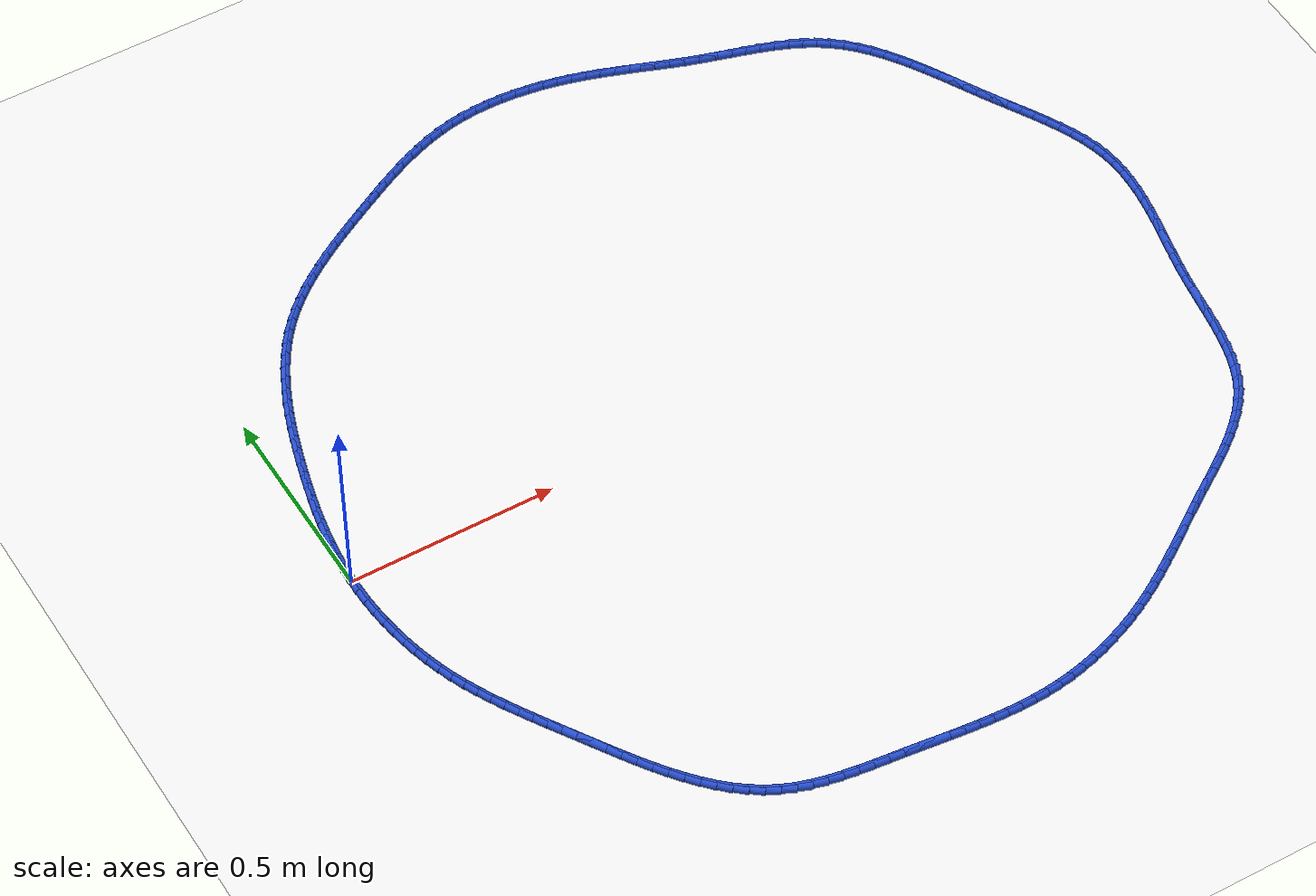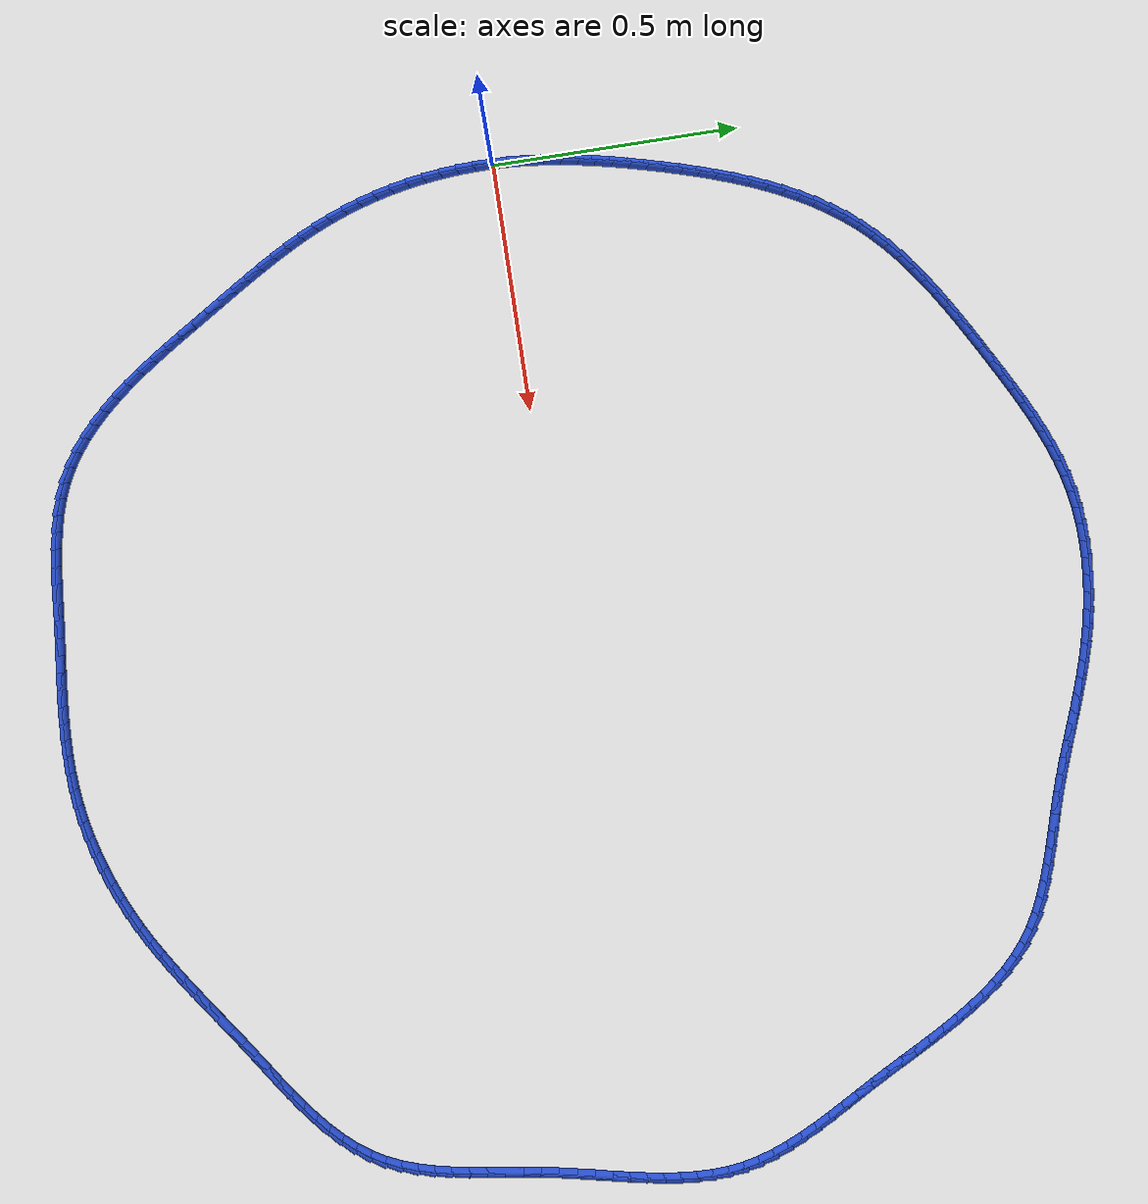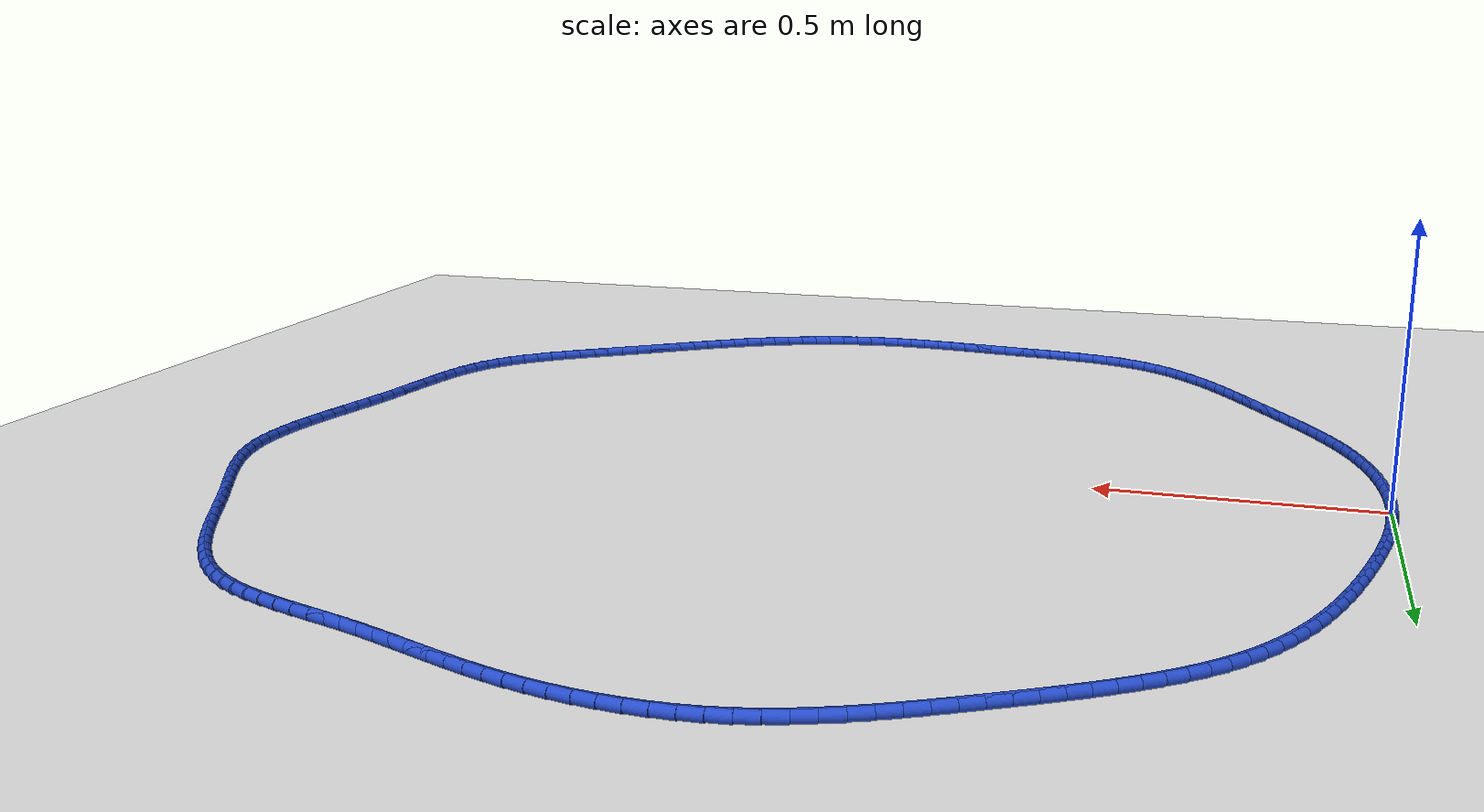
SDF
<sdf version="1.6">
 <world name="default">
  <light name="sun" type="directional">
   <pose>0 0 10 0 -0 0</pose>
   <diffuse>0.8 0.8 0.8 1</diffuse>
   <specular>0.2 0.2 0.2 1</specular>
   <attenuation>
    <range>1000</range>
    <constant>0.9</constant>
    <linear>0.01</linear>
    <quadratic>0.001</quadratic>
   </attenuation>
   <direction>-0.5 0.1 -0.9</direction>
  </light>
  <model name="ground_plane">
   <static>1</static>
   <link name="link">
    <collision name="collision">
     <geometry><plane><normal>0 0 1</normal><size>100 100</size></plane></geometry>
     <surface><friction><ode><mu>100</mu><mu2>50</mu2></ode></friction></surface>
    </collision>
    <visual name="visual">
     <cast_shadows>0</cast_shadows>
     <geometry><plane><normal>0 0 1</normal><size>100 100</size></plane></geometry>
     <material>
      <script><uri>file://media/materials/scripts/gazebo.material</uri><name>Gazebo/WhiteGlow</name></script>
     </material>
    </visual>
   </link>
  </model>
  <gravity>0 0 -9.8</gravity>
  <magnetic_field>6e-06 2.3e-05 -4.2e-05</magnetic_field>
  <atmosphere type="adiabatic"/>
  <physics name="default_physics" default="0" type="ode">
   <max_step_size>0.001</max_step_size>
   <real_time_factor>1</real_time_factor>
   <real_time_update_rate>1000</real_time_update_rate>
  </physics>
  <scene><ambient>0.4 0.4 0.4 1</ambient><background>0.7 0.7 0.7 1</background><shadows>1</shadows></scene>
  <spherical_coordinates>
   <surface_model>EARTH_WGS84</surface_model>
   <latitude_deg>0</latitude_deg>
   <longitude_deg>0</longitude_deg>
   <elevation>0</elevation>
   <heading_deg>0</heading_deg>
  </spherical_coordinates>
  <model name="line">
   <link name="link_0">
    <pose>2.42861286636753e-17 6.938893903907228e-17 0.01 0 1.57 1.5319976299975253</pose>
    <collision name="collision">
     <geometry><cylinder><radius>0.01</radius><length>0.08</length></cylinder></geometry>
    </collision>
    <visual name="visual">
     <material>
      <script><name>Gazebo/Blue</name><uri>file://media/materials/scripts/gazebo.material</uri></script>
     </material>
     <geometry><cylinder><radius>0.01</radius><length>0.08</length></cylinder></geometry>
    </visual>
   </link>
   <link name="link_1">
    <pose>0.0013332961013255368 0.03434721068902115 0.01 0 1.57 1.4957347589479104</pose>
    <collision name="collision">
     <geometry><cylinder><radius>0.01</radius><length>0.08</length></cylinder></geometry>
    </collision>
    <visual name="visual">
     <material>
      <script><name>Gazebo/Blue</name><uri>file://media/materials/scripts/gazebo.material</uri></script>
     </material>
     <geometry><cylinder><radius>0.01</radius><length>0.08</length></cylinder></geometry>
    </visual>
   </link>
   <link name="link_2">
    <pose>0.0039034494445479833 0.06852348291519832 0.01 0 1.57 1.4620143395211584</pose>
    <collision name="collision">
     <geometry><cylinder><radius>0.01</radius><length>0.08</length></cylinder></geometry>
    </collision>
    <visual name="visual">
     <material>
      <script><name>Gazebo/Blue</name><uri>file://media/materials/scripts/gazebo.material</uri></script>
     </material>
     <geometry><cylinder><radius>0.01</radius><length>0.08</length></cylinder></geometry>
    </visual>
   </link>
   <link name="link_3">
    <pose>0.0076203454995357155 0.10255690376160631 0.01 0 1.57 1.430980104530784</pose>
    <collision name="collision">
     <geometry><cylinder><radius>0.01</radius><length>0.08</length></cylinder></geometry>
    </collision>
    <visual name="visual">
     <material>
      <script><name>Gazebo/Blue</name><uri>file://media/materials/scripts/gazebo.material</uri></script>
     </material>
     <geometry><cylinder><radius>0.01</radius><length>0.08</length></cylinder></geometry>
    </visual>
   </link>
   <link name="link_4">
    <pose>0.012393869736157099 0.13647556031132002 0.01 0 1.57 1.4027336423190897</pose>
    <collision name="collision">
     <geometry><cylinder><radius>0.01</radius><length>0.08</length></cylinder></geometry>
    </collision>
    <visual name="visual">
     <material>
      <script><name>Gazebo/Blue</name><uri>file://media/materials/scripts/gazebo.material</uri></script>
     </material>
     <geometry><cylinder><radius>0.01</radius><length>0.08</length></cylinder></geometry>
    </visual>
   </link>
   <link name="link_5">
    <pose>0.01813390762428047 0.17030753964741416 0.01 0 1.57 1.3773396047515634</pose>
    <collision name="collision">
     <geometry><cylinder><radius>0.01</radius><length>0.08</length></cylinder></geometry>
    </collision>
    <visual name="visual">
     <material>
      <script><name>Gazebo/Blue</name><uri>file://media/materials/scripts/gazebo.material</uri></script>
     </material>
     <geometry><cylinder><radius>0.01</radius><length>0.08</length></cylinder></geometry>
    </visual>
   </link>
   <link name="link_6">
    <pose>0.024750344633774186 0.2040809288529636 0.01 0 1.57 1.35483161645047</pose>
    <collision name="collision">
     <geometry><cylinder><radius>0.01</radius><length>0.08</length></cylinder></geometry>
    </collision>
    <visual name="visual">
     <material>
      <script><name>Gazebo/Blue</name><uri>file://media/materials/scripts/gazebo.material</uri></script>
     </material>
     <geometry><cylinder><radius>0.01</radius><length>0.08</length></cylinder></geometry>
    </visual>
   </link>
   <link name="link_7">
    <pose>0.0321530662345066 0.23782381501104302 0.01 0 1.57 1.335218311419584</pose>
    <collision name="collision">
     <geometry><cylinder><radius>0.01</radius><length>0.08</length></cylinder></geometry>
    </collision>
    <visual name="visual">
     <material>
      <script><name>Gazebo/Blue</name><uri>file://media/materials/scripts/gazebo.material</uri></script>
     </material>
     <geometry><cylinder><radius>0.01</radius><length>0.08</length></cylinder></geometry>
    </visual>
   </link>
   <link name="link_8">
    <pose>0.04025195789634607 0.27156428520472736 0.01 0 1.57 1.3184890682118677</pose>
    <collision name="collision">
     <geometry><cylinder><radius>0.01</radius><length>0.08</length></cylinder></geometry>
    </collision>
    <visual name="visual">
     <material>
      <script><name>Gazebo/Blue</name><uri>file://media/materials/scripts/gazebo.material</uri></script>
     </material>
     <geometry><cylinder><radius>0.01</radius><length>0.08</length></cylinder></geometry>
    </visual>
   </link>
   <link name="link_9">
    <pose>0.048956905089160965 0.30533042651709136 0.01 0 1.57 1.3045395421984778</pose>
    <collision name="collision">
     <geometry><cylinder><radius>0.01</radius><length>0.08</length></cylinder></geometry>
    </collision>
    <visual name="visual">
     <material>
      <script><name>Gazebo/Blue</name><uri>file://media/materials/scripts/gazebo.material</uri></script>
     </material>
     <geometry><cylinder><radius>0.01</radius><length>0.08</length></cylinder></geometry>
    </visual>
   </link>
   <link name="link_10">
    <pose>0.05818016048302324 0.3391483987600942 0.01 0 1.57 1.2906812266916168</pose>
    <collision name="collision">
     <geometry><cylinder><radius>0.01</radius><length>0.08</length></cylinder></geometry>
    </collision>
    <visual name="visual">
     <material>
      <script><name>Gazebo/Blue</name><uri>file://media/materials/scripts/gazebo.material</uri></script>
     </material>
     <geometry><cylinder><radius>0.01</radius><length>0.08</length></cylinder></geometry>
    </visual>
   </link>
   <link name="link_11">
    <pose>0.06791284358544548 0.3729801518079231 0.01 0 1.57 1.2736450107143469</pose>
    <collision name="collision">
     <geometry><cylinder><radius>0.01</radius><length>0.08</length></cylinder></geometry>
    </collision>
    <visual name="visual">
     <material>
      <script><name>Gazebo/Blue</name><uri>file://media/materials/scripts/gazebo.material</uri></script>
     </material>
     <geometry><cylinder><radius>0.01</radius><length>0.08</length></cylinder></geometry>
    </visual>
   </link>
   <link name="link_12">
    <pose>0.07824150280431098 0.406709941488023 0.01 0 1.57 1.2531404889853364</pose>
    <collision name="collision">
     <geometry><cylinder><radius>0.01</radius><length>0.08</length></cylinder></geometry>
    </collision>
    <visual name="visual">
     <material>
      <script><name>Gazebo/Blue</name><uri>file://media/materials/scripts/gazebo.material</uri></script>
     </material>
     <geometry><cylinder><radius>0.01</radius><length>0.08</length></cylinder></geometry>
    </visual>
   </link>
   <link name="link_13">
    <pose>0.08925840393630295 0.44021736877935064 0.01 0 1.57 1.2290328772874268</pose>
    <collision name="collision">
     <geometry><cylinder><radius>0.01</radius><length>0.08</length></cylinder></geometry>
    </collision>
    <visual name="visual">
     <material>
      <script><name>Gazebo/Blue</name><uri>file://media/materials/scripts/gazebo.material</uri></script>
     </material>
     <geometry><cylinder><radius>0.01</radius><length>0.08</length></cylinder></geometry>
    </visual>
   </link>
   <link name="link_14">
    <pose>0.10105581277810456 0.4733820346608624 0.01 0 1.57 1.201155934864987</pose>
    <collision name="collision">
     <geometry><cylinder><radius>0.01</radius><length>0.08</length></cylinder></geometry>
    </collision>
    <visual name="visual">
     <material>
      <script><name>Gazebo/Blue</name><uri>file://media/materials/scripts/gazebo.material</uri></script>
     </material>
     <geometry><cylinder><radius>0.01</radius><length>0.08</length></cylinder></geometry>
    </visual>
   </link>
   <link name="link_15">
    <pose>0.11372599512639905 0.5060835401115151 0.01 0 1.57 1.1693188276299384</pose>
    <collision name="collision">
     <geometry><cylinder><radius>0.01</radius><length>0.08</length></cylinder></geometry>
    </collision>
    <visual name="visual">
     <material>
      <script><name>Gazebo/Blue</name><uri>file://media/materials/scripts/gazebo.material</uri></script>
     </material>
     <geometry><cylinder><radius>0.01</radius><length>0.08</length></cylinder></geometry>
    </visual>
   </link>
   <link name="link_16">
    <pose>0.12736121677786955 0.538201486110265 0.01 0 1.57 1.1333156140355276</pose>
    <collision name="collision">
     <geometry><cylinder><radius>0.01</radius><length>0.08</length></cylinder></geometry>
    </collision>
    <visual name="visual">
     <material>
      <script><name>Gazebo/Blue</name><uri>file://media/materials/scripts/gazebo.material</uri></script>
     </material>
     <geometry><cylinder><radius>0.01</radius><length>0.08</length></cylinder></geometry>
    </visual>
   </link>
   <link name="link_17">
    <pose>0.1420537435291994 0.5696154736360691 0.01 0 1.57 1.09293848286722</pose>
    <collision name="collision">
     <geometry><cylinder><radius>0.01</radius><length>0.08</length></cylinder></geometry>
    </collision>
    <visual name="visual">
     <material>
      <script><name>Gazebo/Blue</name><uri>file://media/materials/scripts/gazebo.material</uri></script>
     </material>
     <geometry><cylinder><radius>0.01</radius><length>0.08</length></cylinder></geometry>
    </visual>
   </link>
   <link name="link_18">
    <pose>0.15789584117707167 0.6002051036678836 0.01 0 1.57 1.0479958990652938</pose>
    <collision name="collision">
     <geometry><cylinder><radius>0.01</radius><length>0.08</length></cylinder></geometry>
    </collision>
    <visual name="visual">
     <material>
      <script><name>Gazebo/Blue</name><uri>file://media/materials/scripts/gazebo.material</uri></script>
     </material>
     <geometry><cylinder><radius>0.01</radius><length>0.08</length></cylinder></geometry>
    </visual>
   </link>
   <link name="link_19">
    <pose>0.1749797755181695 0.629849977184665 0.01 0 1.57 0.9983366031011226</pose>
    <collision name="collision">
     <geometry><cylinder><radius>0.01</radius><length>0.08</length></cylinder></geometry>
    </collision>
    <visual name="visual">
     <material>
      <script><name>Gazebo/Blue</name><uri>file://media/materials/scripts/gazebo.material</uri></script>
     </material>
     <geometry><cylinder><radius>0.01</radius><length>0.08</length></cylinder></geometry>
    </visual>
   </link>
   <link name="link_20">
    <pose>0.19339781234917627 0.6584296951653701 0.01 0 1.57 0.9438797772226359</pose>
    <collision name="collision">
     <geometry><cylinder><radius>0.01</radius><length>0.08</length></cylinder></geometry>
    </collision>
    <visual name="visual">
     <material>
      <script><name>Gazebo/Blue</name><uri>file://media/materials/scripts/gazebo.material</uri></script>
     </material>
     <geometry><cylinder><radius>0.01</radius><length>0.08</length></cylinder></geometry>
    </visual>
   </link>
   <link name="link_21">
    <pose>0.21324221746677507 0.6858238585889553 0.01 0 1.57 0.8846511445592343</pose>
    <collision name="collision">
     <geometry><cylinder><radius>0.01</radius><length>0.08</length></cylinder></geometry>
    </collision>
    <visual name="visual">
     <material>
      <script><name>Gazebo/Blue</name><uri>file://media/materials/scripts/gazebo.material</uri></script>
     </material>
     <geometry><cylinder><radius>0.01</radius><length>0.08</length></cylinder></geometry>
    </visual>
   </link>
   <link name="link_22">
    <pose>0.2346052398212903 0.7119120853132177 0.01 0 1.57 0.822889807444845</pose>
    <collision name="collision">
     <geometry><cylinder><radius>0.01</radius><length>0.08</length></cylinder></geometry>
    </collision>
    <visual name="visual">
     <material>
      <script><name>Gazebo/Blue</name><uri>file://media/materials/scripts/gazebo.material</uri></script>
     </material>
     <geometry><cylinder><radius>0.01</radius><length>0.08</length></cylinder></geometry>
    </visual>
   </link>
   <link name="link_23">
    <pose>0.25752979301968654 0.7366234236621726 0.01 0 1.57 0.765528614406891</pose>
    <collision name="collision">
     <geometry><cylinder><radius>0.01</radius><length>0.08</length></cylinder></geometry>
    </collision>
    <visual name="visual">
     <material>
      <script><name>Gazebo/Blue</name><uri>file://media/materials/scripts/gazebo.material</uri></script>
     </material>
     <geometry><cylinder><radius>0.01</radius><length>0.08</length></cylinder></geometry>
    </visual>
   </link>
   <link name="link_24">
    <pose>0.2819010662322203 0.7600449505030605 0.01 0 1.57 0.7141234712473254</pose>
    <collision name="collision">
     <geometry><cylinder><radius>0.01</radius><length>0.08</length></cylinder></geometry>
    </collision>
    <visual name="visual">
     <material>
      <script><name>Gazebo/Blue</name><uri>file://media/materials/scripts/gazebo.material</uri></script>
     </material>
     <geometry><cylinder><radius>0.01</radius><length>0.08</length></cylinder></geometry>
    </visual>
   </link>
   <link name="link_25">
    <pose>0.30757279584087693 0.7822952561351211 0.01 0 1.57 0.6687328194360634</pose>
    <collision name="collision">
     <geometry><cylinder><radius>0.01</radius><length>0.08</length></cylinder></geometry>
    </collision>
    <visual name="visual">
     <material>
      <script><name>Gazebo/Blue</name><uri>file://media/materials/scripts/gazebo.material</uri></script>
     </material>
     <geometry><cylinder><radius>0.01</radius><length>0.08</length></cylinder></geometry>
    </visual>
   </link>
   <link name="link_26">
    <pose>0.33439871822764244 0.8034929308575938 0.01 0 1.57 0.6292856563128225</pose>
    <collision name="collision">
     <geometry><cylinder><radius>0.01</radius><length>0.08</length></cylinder></geometry>
    </collision>
    <visual name="visual">
     <material>
      <script><name>Gazebo/Blue</name><uri>file://media/materials/scripts/gazebo.material</uri></script>
     </material>
     <geometry><cylinder><radius>0.01</radius><length>0.08</length></cylinder></geometry>
    </visual>
   </link>
   <link name="link_27">
    <pose>0.362232569774502 0.8237565649697183 0.01 0 1.57 0.5956316358570476</pose>
    <collision name="collision">
     <geometry><cylinder><radius>0.01</radius><length>0.08</length></cylinder></geometry>
    </collision>
    <visual name="visual">
     <material>
      <script><name>Gazebo/Blue</name><uri>file://media/materials/scripts/gazebo.material</uri></script>
     </material>
     <geometry><cylinder><radius>0.01</radius><length>0.08</length></cylinder></geometry>
    </visual>
   </link>
   <link name="link_28">
    <pose>0.39092808686344144 0.8432047487707338 0.01 0 1.57 0.567582661008649</pose>
    <collision name="collision">
     <geometry><cylinder><radius>0.01</radius><length>0.08</length></cylinder></geometry>
    </collision>
    <visual name="visual">
     <material>
      <script><name>Gazebo/Blue</name><uri>file://media/materials/scripts/gazebo.material</uri></script>
     </material>
     <geometry><cylinder><radius>0.01</radius><length>0.08</length></cylinder></geometry>
    </visual>
   </link>
   <link name="link_29">
    <pose>0.4203390058764466 0.8619560725598802 0.01 0 1.57 0.5449449606191419</pose>
    <collision name="collision">
     <geometry><cylinder><radius>0.01</radius><length>0.08</length></cylinder></geometry>
    </collision>
    <visual name="visual">
     <material>
      <script><name>Gazebo/Blue</name><uri>file://media/materials/scripts/gazebo.material</uri></script>
     </material>
     <geometry><cylinder><radius>0.01</radius><length>0.08</length></cylinder></geometry>
    </visual>
   </link>
   <link name="link_30">
    <pose>0.4503190631955027 0.8801291266363965 0.01 0 1.57 0.5275425074604615</pose>
    <collision name="collision">
     <geometry><cylinder><radius>0.01</radius><length>0.08</length></cylinder></geometry>
    </collision>
    <visual name="visual">
     <material>
      <script><name>Gazebo/Blue</name><uri>file://media/materials/scripts/gazebo.material</uri></script>
     </material>
     <geometry><cylinder><radius>0.01</radius><length>0.08</length></cylinder></geometry>
    </visual>
   </link>
   <link name="link_31">
    <pose>0.4807219952025956 0.8978425012995228 0.01 0 1.57 0.5152334188689925</pose>
    <collision name="collision">
     <geometry><cylinder><radius>0.01</radius><length>0.08</length></cylinder></geometry>
    </collision>
    <visual name="visual">
     <material>
      <script><name>Gazebo/Blue</name><uri>file://media/materials/scripts/gazebo.material</uri></script>
     </material>
     <geometry><cylinder><radius>0.01</radius><length>0.08</length></cylinder></geometry>
    </visual>
   </link>
   <link name="link_32">
    <pose>0.5114015382797108 0.9152147868484983 0.01 0 1.57 0.5079189197216724</pose>
    <collision name="collision">
     <geometry><cylinder><radius>0.01</radius><length>0.08</length></cylinder></geometry>
    </collision>
    <visual name="visual">
     <material>
      <script><name>Gazebo/Blue</name><uri>file://media/materials/scripts/gazebo.material</uri></script>
     </material>
     <geometry><cylinder><radius>0.01</radius><length>0.08</length></cylinder></geometry>
    </visual>
   </link>
   <link name="link_33">
    <pose>0.5422114681492941 0.9323645081079053 0.01 0 1.57 0.5029805812934454</pose>
    <collision name="collision">
     <geometry><cylinder><radius>0.01</radius><length>0.08</length></cylinder></geometry>
    </collision>
    <visual name="visual">
     <material>
      <script><name>Gazebo/Blue</name><uri>file://media/materials/scripts/gazebo.material</uri></script>
     </material>
     <geometry><cylinder><radius>0.01</radius><length>0.08</length></cylinder></geometry>
    </visual>
   </link>
   <link name="link_34">
    <pose>0.5730522624212273 0.9493324635605214 0.01 0 1.57 0.492822098935053</pose>
    <collision name="collision">
     <geometry><cylinder><radius>0.01</radius><length>0.08</length></cylinder></geometry>
    </collision>
    <visual name="visual">
     <material>
      <script><name>Gazebo/Blue</name><uri>file://media/materials/scripts/gazebo.material</uri></script>
     </material>
     <geometry><cylinder><radius>0.01</radius><length>0.08</length></cylinder></geometry>
    </visual>
   </link>
   <link name="link_35">
    <pose>0.6039614878840294 0.9659312930227029 0.01 0 1.57 0.47595645030181616</pose>
    <collision name="collision">
     <geometry><cylinder><radius>0.01</radius><length>0.08</length></cylinder></geometry>
    </collision>
    <visual name="visual">
     <material>
      <script><name>Gazebo/Blue</name><uri>file://media/materials/scripts/gazebo.material</uri></script>
     </material>
     <geometry><cylinder><radius>0.01</radius><length>0.08</length></cylinder></geometry>
    </visual>
   </link>
   <link name="link_36">
    <pose>0.6350017367816518 0.9819319862360545 0.01 0 1.57 0.45222671723746927</pose>
    <collision name="collision">
     <geometry><cylinder><radius>0.01</radius><length>0.08</length></cylinder></geometry>
    </collision>
    <visual name="visual">
     <material>
      <script><name>Gazebo/Blue</name><uri>file://media/materials/scripts/gazebo.material</uri></script>
     </material>
     <geometry><cylinder><radius>0.01</radius><length>0.08</length></cylinder></geometry>
    </visual>
   </link>
   <link name="link_37">
    <pose>0.6662356013580458 0.9971055329421803 0.01 0 1.57 0.4214496296331358</pose>
    <collision name="collision">
     <geometry><cylinder><radius>0.01</radius><length>0.08</length></cylinder></geometry>
    </collision>
    <visual name="visual">
     <material>
      <script><name>Gazebo/Blue</name><uri>file://media/materials/scripts/gazebo.material</uri></script>
     </material>
     <geometry><cylinder><radius>0.01</radius><length>0.08</length></cylinder></geometry>
    </visual>
   </link>
   <link name="link_38">
    <pose>0.6977256738571628 1.0112229228826846 0.01 0 1.57 0.383448130057976</pose>
    <collision name="collision">
     <geometry><cylinder><radius>0.01</radius><length>0.08</length></cylinder></geometry>
    </collision>
    <visual name="visual">
     <material>
      <script><name>Gazebo/Blue</name><uri>file://media/materials/scripts/gazebo.material</uri></script>
     </material>
     <geometry><cylinder><radius>0.01</radius><length>0.08</length></cylinder></geometry>
    </visual>
   </link>
   <link name="link_39">
    <pose>0.7295345465229549 1.0240551457991727 0.01 0 1.57 0.3380980717340698</pose>
    <collision name="collision">
     <geometry><cylinder><radius>0.01</radius><length>0.08</length></cylinder></geometry>
    </collision>
    <visual name="visual">
     <material>
      <script><name>Gazebo/Blue</name><uri>file://media/materials/scripts/gazebo.material</uri></script>
     </material>
     <geometry><cylinder><radius>0.01</radius><length>0.08</length></cylinder></geometry>
    </visual>
   </link>
   <link name="link_40">
    <pose>0.7617248115993724 1.0353731914332478 0.01 0 1.57 0.2853899355566183</pose>
    <collision name="collision">
     <geometry><cylinder><radius>0.01</radius><length>0.08</length></cylinder></geometry>
    </collision>
    <visual name="visual">
     <material>
      <script><name>Gazebo/Blue</name><uri>file://media/materials/scripts/gazebo.material</uri></script>
     </material>
     <geometry><cylinder><radius>0.01</radius><length>0.08</length></cylinder></geometry>
    </visual>
   </link>
   <link name="link_41">
    <pose>0.7943590613303679 1.0449480495265153 0.01 0 1.57 0.22550289226012357</pose>
    <collision name="collision">
     <geometry><cylinder><radius>0.01</radius><length>0.08</length></cylinder></geometry>
    </collision>
    <visual name="visual">
     <material>
      <script><name>Gazebo/Blue</name><uri>file://media/materials/scripts/gazebo.material</uri></script>
     </material>
     <geometry><cylinder><radius>0.01</radius><length>0.08</length></cylinder></geometry>
    </visual>
   </link>
   <link name="link_42">
    <pose>0.8274998879598919 1.0525507098205793 0.01 0 1.57 0.16003872639094327</pose>
    <collision name="collision">
     <geometry><cylinder><radius>0.01</radius><length>0.08</length></cylinder></geometry>
    </collision>
    <visual name="visual">
     <material>
      <script><name>Gazebo/Blue</name><uri>file://media/materials/scripts/gazebo.material</uri></script>
     </material>
     <geometry><cylinder><radius>0.01</radius><length>0.08</length></cylinder></geometry>
    </visual>
   </link>
   <link name="link_43">
    <pose>0.8611893692728201 1.057988838805704 0.01 0 1.57 0.09652674588150013</pose>
    <collision name="collision">
     <geometry><cylinder><radius>0.01</radius><length>0.08</length></cylinder></geometry>
    </collision>
    <visual name="visual">
     <material>
      <script><name>Gazebo/Blue</name><uri>file://media/materials/scripts/gazebo.material</uri></script>
     </material>
     <geometry><cylinder><radius>0.01</radius><length>0.08</length></cylinder></geometry>
    </visual>
   </link>
   <link name="link_44">
    <pose>0.8953432967875705 1.0612958837074293 0.01 0 1.57 0.03754103086216427</pose>
    <collision name="collision">
     <geometry><cylinder><radius>0.01</radius><length>0.08</length></cylinder></geometry>
    </collision>
    <visual name="visual">
     <material>
      <script><name>Gazebo/Blue</name><uri>file://media/materials/scripts/gazebo.material</uri></script>
     </material>
     <geometry><cylinder><radius>0.01</radius><length>0.08</length></cylinder></geometry>
    </visual>
   </link>
   <link name="link_45">
    <pose>0.9298294456153159 1.0625911378217943 0.01 0 1.57 -0.01721204589838933</pose>
    <collision name="collision">
     <geometry><cylinder><radius>0.01</radius><length>0.08</length></cylinder></geometry>
    </collision>
    <visual name="visual">
     <material>
      <script><name>Gazebo/Blue</name><uri>file://media/materials/scripts/gazebo.material</uri></script>
     </material>
     <geometry><cylinder><radius>0.01</radius><length>0.08</length></cylinder></geometry>
    </visual>
   </link>
   <link name="link_46">
    <pose>0.9645154977428514 1.0619940609371339 0.01 0 1.57 -0.06808739640966668</pose>
    <collision name="collision">
     <geometry><cylinder><radius>0.01</radius><length>0.08</length></cylinder></geometry>
    </collision>
    <visual name="visual">
     <material>
      <script><name>Gazebo/Blue</name><uri>file://media/materials/scripts/gazebo.material</uri></script>
     </material>
     <geometry><cylinder><radius>0.01</radius><length>0.08</length></cylinder></geometry>
    </visual>
   </link>
   <link name="link_47">
    <pose>0.9992691351569707 1.0596241128417834 0.01 0 1.57 -0.11546811987904403</pose>
    <collision name="collision">
     <geometry><cylinder><radius>0.01</radius><length>0.08</length></cylinder></geometry>
    </collision>
    <visual name="visual">
     <material>
      <script><name>Gazebo/Blue</name><uri>file://media/materials/scripts/gazebo.material</uri></script>
     </material>
     <geometry><cylinder><radius>0.01</radius><length>0.08</length></cylinder></geometry>
    </visual>
   </link>
   <link name="link_48">
    <pose>1.0339580398444692 1.055600753324078 0.01 0 1.57 -0.15974665244853856</pose>
    <collision name="collision">
     <geometry><cylinder><radius>0.01</radius><length>0.08</length></cylinder></geometry>
    </collision>
    <visual name="visual">
     <material>
      <script><name>Gazebo/Blue</name><uri>file://media/materials/scripts/gazebo.material</uri></script>
     </material>
     <geometry><cylinder><radius>0.01</radius><length>0.08</length></cylinder></geometry>
    </visual>
   </link>
   <link name="link_49">
    <pose>1.068449893792141 1.0500434421723535 0.01 0 1.57 -0.20131337771642985</pose>
    <collision name="collision">
     <geometry><cylinder><radius>0.01</radius><length>0.08</length></cylinder></geometry>
    </collision>
    <visual name="visual">
     <material>
      <script><name>Gazebo/Blue</name><uri>file://media/materials/scripts/gazebo.material</uri></script>
     </material>
     <geometry><cylinder><radius>0.01</radius><length>0.08</length></cylinder></geometry>
    </visual>
   </link>
   <link name="link_50">
    <pose>1.1026123789867812 1.0430716391749448 0.01 0 1.57 -0.2405510826231445</pose>
    <collision name="collision">
     <geometry><cylinder><radius>0.01</radius><length>0.08</length></cylinder></geometry>
    </collision>
    <visual name="visual">
     <material>
      <script><name>Gazebo/Blue</name><uri>file://media/materials/scripts/gazebo.material</uri></script>
     </material>
     <geometry><cylinder><radius>0.01</radius><length>0.08</length></cylinder></geometry>
    </visual>
   </link>
   <link name="link_51">
    <pose>1.136313177415184 1.0348048041201874 0.01 0 1.57 -0.27717214346277813</pose>
    <collision name="collision">
     <geometry><cylinder><radius>0.01</radius><length>0.08</length></cylinder></geometry>
    </collision>
    <visual name="visual">
     <material>
      <script><name>Gazebo/Blue</name><uri>file://media/materials/scripts/gazebo.material</uri></script>
     </material>
     <geometry><cylinder><radius>0.01</radius><length>0.08</length></cylinder></geometry>
    </visual>
   </link>
   <link name="link_52">
    <pose>1.1694566323345672 1.0253756529250417 0.01 0 1.57 -0.30807189492269993</pose>
    <collision name="collision">
     <geometry><cylinder><radius>0.01</radius><length>0.08</length></cylinder></geometry>
    </collision>
    <visual name="visual">
     <material>
      <script><name>Gazebo/Blue</name><uri>file://media/materials/scripts/gazebo.material</uri></script>
     </material>
     <geometry><cylinder><radius>0.01</radius><length>0.08</length></cylinder></geometry>
    </visual>
   </link>
   <link name="link_53">
    <pose>1.2021239006334863 1.0149808344856774 0.01 0 1.57 -0.3320006440965367</pose>
    <collision name="collision">
     <geometry><cylinder><radius>0.01</radius><length>0.08</length></cylinder></geometry>
    </collision>
    <visual name="visual">
     <material>
      <script><name>Gazebo/Blue</name><uri>file://media/materials/scripts/gazebo.material</uri></script>
     </material>
     <geometry><cylinder><radius>0.01</radius><length>0.08</length></cylinder></geometry>
    </visual>
   </link>
   <link name="link_54">
    <pose>1.234449374755906 1.0038362468230708 0.01 0 1.57 -0.3487476856497626</pose>
    <collision name="collision">
     <geometry><cylinder><radius>0.01</radius><length>0.08</length></cylinder></geometry>
    </collision>
    <visual name="visual">
     <material>
      <script><name>Gazebo/Blue</name><uri>file://media/materials/scripts/gazebo.material</uri></script>
     </material>
     <geometry><cylinder><radius>0.01</radius><length>0.08</length></cylinder></geometry>
    </visual>
   </link>
   <link name="link_55">
    <pose>1.266567457854092 0.9921577918301479 0.01 0 1.57 -0.35820996493097723</pose>
    <collision name="collision">
     <geometry><cylinder><radius>0.01</radius><length>0.08</length></cylinder></geometry>
    </collision>
    <visual name="visual">
     <material>
      <script><name>Gazebo/Blue</name><uri>file://media/materials/scripts/gazebo.material</uri></script>
     </material>
     <geometry><cylinder><radius>0.01</radius><length>0.08</length></cylinder></geometry>
    </visual>
   </link>
   <link name="link_56">
    <pose>1.298612553080311 0.980161371399836 0.01 0 1.57 -0.3603682954343708</pose>
    <collision name="collision">
     <geometry><cylinder><radius>0.01</radius><length>0.08</length></cylinder></geometry>
    </collision>
    <visual name="visual">
     <material>
      <script><name>Gazebo/Blue</name><uri>file://media/materials/scripts/gazebo.material</uri></script>
     </material>
     <geometry><cylinder><radius>0.01</radius><length>0.08</length></cylinder></geometry>
    </visual>
   </link>
   <link name="link_57">
    <pose>1.3307190635868293 0.9680628874250607 0.01 0 1.57 -0.3552723225432319</pose>
    <collision name="collision">
     <geometry><cylinder><radius>0.01</radius><length>0.08</length></cylinder></geometry>
    </collision>
    <visual name="visual">
     <material>
      <script><name>Gazebo/Blue</name><uri>file://media/materials/scripts/gazebo.material</uri></script>
     </material>
     <geometry><cylinder><radius>0.01</radius><length>0.08</length></cylinder></geometry>
    </visual>
   </link>
   <link name="link_58">
    <pose>1.3630213925259138 0.9560782417987496 0.01 0 1.57 -0.34303543803610054</pose>
    <collision name="collision">
     <geometry><cylinder><radius>0.01</radius><length>0.08</length></cylinder></geometry>
    </collision>
    <visual name="visual">
     <material>
      <script><name>Gazebo/Blue</name><uri>file://media/materials/scripts/gazebo.material</uri></script>
     </material>
     <geometry><cylinder><radius>0.01</radius><length>0.08</length></cylinder></geometry>
    </visual>
   </link>
   <link name="link_59">
    <pose>1.3956539430498296 0.9444233364138287 0.01 0 1.57 -0.32384153242769537</pose>
    <collision name="collision">
     <geometry><cylinder><radius>0.01</radius><length>0.08</length></cylinder></geometry>
    </collision>
    <visual name="visual">
     <material>
      <script><name>Gazebo/Blue</name><uri>file://media/materials/scripts/gazebo.material</uri></script>
     </material>
     <geometry><cylinder><radius>0.01</radius><length>0.08</length></cylinder></geometry>
    </visual>
   </link>
   <link name="link_60">
    <pose>1.4287510728277324 0.9333140112194862 0.01 0 1.57 -0.3021883758827398</pose>
    <collision name="collision">
     <geometry><cylinder><radius>0.01</radius><length>0.08</length></cylinder></geometry>
    </collision>
    <visual name="visual">
     <material>
      <script><name>Gazebo/Blue</name><uri>file://media/materials/scripts/gazebo.material</uri></script>
     </material>
     <geometry><cylinder><radius>0.01</radius><length>0.08</length></cylinder></geometry>
    </visual>
   </link>
   <link name="link_61">
    <pose>1.4623537142717886 0.9228388697152982 0.01 0 1.57 -0.2911663075131773</pose>
    <collision name="collision">
     <geometry><cylinder><radius>0.01</radius><length>0.08</length></cylinder></geometry>
    </collision>
    <visual name="visual">
     <material>
      <script><name>Gazebo/Blue</name><uri>file://media/materials/scripts/gazebo.material</uri></script>
     </material>
     <geometry><cylinder><radius>0.01</radius><length>0.08</length></cylinder></geometry>
    </visual>
   </link>
   <link name="link_62">
    <pose>1.496212981181234 0.9126918095950457 0.01 0 1.57 -0.2930324917197571</pose>
    <collision name="collision">
     <geometry><cylinder><radius>0.01</radius><length>0.08</length></cylinder></geometry>
    </collision>
    <visual name="visual">
     <material>
      <script><name>Gazebo/Blue</name><uri>file://media/materials/scripts/gazebo.material</uri></script>
     </material>
     <geometry><cylinder><radius>0.01</radius><length>0.08</length></cylinder></geometry>
    </visual>
   </link>
   <link name="link_63">
    <pose>1.530023955913463 0.9024904189767451 0.01 0 1.57 -0.30784868390508313</pose>
    <collision name="collision">
     <geometry><cylinder><radius>0.01</radius><length>0.08</length></cylinder></geometry>
    </collision>
    <visual name="visual">
     <material>
      <script><name>Gazebo/Blue</name><uri>file://media/materials/scripts/gazebo.material</uri></script>
     </material>
     <geometry><cylinder><radius>0.01</radius><length>0.08</length></cylinder></geometry>
    </visual>
   </link>
   <link name="link_64">
    <pose>1.5634817208258716 0.8918522859784112 0.01 0 1.57 -0.33606123515005626</pose>
    <collision name="collision">
     <geometry><cylinder><radius>0.01</radius><length>0.08</length></cylinder></geometry>
    </collision>
    <visual name="visual">
     <material>
      <script><name>Gazebo/Blue</name><uri>file://media/materials/scripts/gazebo.material</uri></script>
     </material>
     <geometry><cylinder><radius>0.01</radius><length>0.08</length></cylinder></geometry>
    </visual>
   </link>
   <link name="link_65">
    <pose>1.5962813582758537 0.8803949987180599 0.01 0 1.57 -0.37845263314272626</pose>
    <collision name="collision">
     <geometry><cylinder><radius>0.01</radius><length>0.08</length></cylinder></geometry>
    </collision>
    <visual name="visual">
     <material>
      <script><name>Gazebo/Blue</name><uri>file://media/materials/scripts/gazebo.material</uri></script>
     </material>
     <geometry><cylinder><radius>0.01</radius><length>0.08</length></cylinder></geometry>
    </visual>
   </link>
   <link name="link_66">
    <pose>1.6281179506208043 0.8677361453137069 0.01 0 1.57 -0.436021789033788</pose>
    <collision name="collision">
     <geometry><cylinder><radius>0.01</radius><length>0.08</length></cylinder></geometry>
    </collision>
    <visual name="visual">
     <material>
      <script><name>Gazebo/Blue</name><uri>file://media/materials/scripts/gazebo.material</uri></script>
     </material>
     <geometry><cylinder><radius>0.01</radius><length>0.08</length></cylinder></geometry>
    </visual>
   </link>
   <link name="link_67">
    <pose>1.6586865802181174 0.853493313883367 0.01 0 1.57 -0.5097424317279889</pose>
    <collision name="collision">
     <geometry><cylinder><radius>0.01</radius><length>0.08</length></cylinder></geometry>
    </collision>
    <visual name="visual">
     <material>
      <script><name>Gazebo/Blue</name><uri>file://media/materials/scripts/gazebo.material</uri></script>
     </material>
     <geometry><cylinder><radius>0.01</radius><length>0.08</length></cylinder></geometry>
    </visual>
   </link>
   <link name="link_68">
    <pose>1.6876823294251884 0.8372840925450558 0.01 0 1.57 -0.5996519968335257</pose>
    <collision name="collision">
     <geometry><cylinder><radius>0.01</radius><length>0.08</length></cylinder></geometry>
    </collision>
    <visual name="visual">
     <material>
      <script><name>Gazebo/Blue</name><uri>file://media/materials/scripts/gazebo.material</uri></script>
     </material>
     <geometry><cylinder><radius>0.01</radius><length>0.08</length></cylinder></geometry>
    </visual>
   </link>
   <link name="link_69">
    <pose>1.7148104996016462 0.8187385688252817 0.01 0 1.57 -0.6935753661152109</pose>
    <collision name="collision">
     <geometry><cylinder><radius>0.01</radius><length>0.08</length></cylinder></geometry>
    </collision>
    <visual name="visual">
     <material>
      <script><name>Gazebo/Blue</name><uri>file://media/materials/scripts/gazebo.material</uri></script>
     </material>
     <geometry><cylinder><radius>0.01</radius><length>0.08</length></cylinder></geometry>
    </visual>
   </link>
   <link name="link_70">
    <pose>1.7400177993070385 0.7977821083154447 0.01 0 1.57 -0.7781958988368085</pose>
    <collision name="collision">
     <geometry><cylinder><radius>0.01</radius><length>0.08</length></cylinder></geometry>
    </collision>
    <visual name="visual">
     <material>
      <script><name>Gazebo/Blue</name><uri>file://media/materials/scripts/gazebo.material</uri></script>
     </material>
     <geometry><cylinder><radius>0.01</radius><length>0.08</length></cylinder></geometry>
    </visual>
   </link>
   <link name="link_71">
    <pose>1.763495937218761 0.7746397493620243 0.01 0 1.57 -0.8520112085431466</pose>
    <collision name="collision">
     <geometry><cylinder><radius>0.01</radius><length>0.08</length></cylinder></geometry>
    </collision>
    <visual name="visual">
     <material>
      <script><name>Gazebo/Blue</name><uri>file://media/materials/scripts/gazebo.material</uri></script>
     </material>
     <geometry><cylinder><radius>0.01</radius><length>0.08</length></cylinder></geometry>
    </visual>
   </link>
   <link name="link_72">
    <pose>1.7854475596491923 0.7495499087181665 0.01 0 1.57 -0.9147910774339232</pose>
    <collision name="collision">
     <geometry><cylinder><radius>0.01</radius><length>0.08</length></cylinder></geometry>
    </collision>
    <visual name="visual">
     <material>
      <script><name>Gazebo/Blue</name><uri>file://media/materials/scripts/gazebo.material</uri></script>
     </material>
     <geometry><cylinder><radius>0.01</radius><length>0.08</length></cylinder></geometry>
    </visual>
   </link>
   <link name="link_73">
    <pose>1.806075312910712 0.722751003137018 0.01 0 1.57 -0.9668004484924682</pose>
    <collision name="collision">
     <geometry><cylinder><radius>0.01</radius><length>0.08</length></cylinder></geometry>
    </collision>
    <visual name="visual">
     <material>
      <script><name>Gazebo/Blue</name><uri>file://media/materials/scripts/gazebo.material</uri></script>
     </material>
     <geometry><cylinder><radius>0.01</radius><length>0.08</length></cylinder></geometry>
    </visual>
   </link>
   <link name="link_74">
    <pose>1.8255818433156985 0.6944814493717238 0.01 0 1.57 -1.0085651982869297</pose>
    <collision name="collision">
     <geometry><cylinder><radius>0.01</radius><length>0.08</length></cylinder></geometry>
    </collision>
    <visual name="visual">
     <material>
      <script><name>Gazebo/Blue</name><uri>file://media/materials/scripts/gazebo.material</uri></script>
     </material>
     <geometry><cylinder><radius>0.01</radius><length>0.08</length></cylinder></geometry>
    </visual>
   </link>
   <link name="link_75">
    <pose>1.8441697971765318 0.6649796641754306 0.01 0 1.57 -1.0406954445964798</pose>
    <collision name="collision">
     <geometry><cylinder><radius>0.01</radius><length>0.08</length></cylinder></geometry>
    </collision>
    <visual name="visual">
     <material>
      <script><name>Gazebo/Blue</name><uri>file://media/materials/scripts/gazebo.material</uri></script>
     </material>
     <geometry><cylinder><radius>0.01</radius><length>0.08</length></cylinder></geometry>
    </visual>
   </link>
   <link name="link_76">
    <pose>1.862041820805591 0.6344840643012849 0.01 0 1.57 -1.0637693654418112</pose>
    <collision name="collision">
     <geometry><cylinder><radius>0.01</radius><length>0.08</length></cylinder></geometry>
    </collision>
    <visual name="visual">
     <material>
      <script><name>Gazebo/Blue</name><uri>file://media/materials/scripts/gazebo.material</uri></script>
     </material>
     <geometry><cylinder><radius>0.01</radius><length>0.08</length></cylinder></geometry>
    </visual>
   </link>
   <link name="link_77">
    <pose>1.8794005605152555 0.6032330665024317 0.01 0 1.57 -1.0782648698435238</pose>
    <collision name="collision">
     <geometry><cylinder><radius>0.01</radius><length>0.08</length></cylinder></geometry>
    </collision>
    <visual name="visual">
     <material>
      <script><name>Gazebo/Blue</name><uri>file://media/materials/scripts/gazebo.material</uri></script>
     </material>
     <geometry><cylinder><radius>0.01</radius><length>0.08</length></cylinder></geometry>
    </visual>
   </link>
   <link name="link_78">
    <pose>1.8964486626179038 0.5714650875320177 0.01 0 1.57 -1.0845238505308503</pose>
    <collision name="collision">
     <geometry><cylinder><radius>0.01</radius><length>0.08</length></cylinder></geometry>
    </collision>
    <visual name="visual">
     <material>
      <script><name>Gazebo/Blue</name><uri>file://media/materials/scripts/gazebo.material</uri></script>
     </material>
     <geometry><cylinder><radius>0.01</radius><length>0.08</length></cylinder></geometry>
    </visual>
   </link>
   <link name="link_79">
    <pose>1.913388773425916 0.5394185441431892 0.01 0 1.57 -1.0827367992076897</pose>
    <collision name="collision">
     <geometry><cylinder><radius>0.01</radius><length>0.08</length></cylinder></geometry>
    </collision>
    <visual name="visual">
     <material>
      <script><name>Gazebo/Blue</name><uri>file://media/materials/scripts/gazebo.material</uri></script>
     </material>
     <geometry><cylinder><radius>0.01</radius><length>0.08</length></cylinder></geometry>
    </visual>
   </link>
   <link name="link_80">
    <pose>1.9304235392516698 0.507331853089092 0.01 0 1.57 -1.0730169813747679</pose>
    <collision name="collision">
     <geometry><cylinder><radius>0.01</radius><length>0.08</length></cylinder></geometry>
    </collision>
    <visual name="visual">
     <material>
      <script><name>Gazebo/Blue</name><uri>file://media/materials/scripts/gazebo.material</uri></script>
     </material>
     <geometry><cylinder><radius>0.01</radius><length>0.08</length></cylinder></geometry>
    </visual>
   </link>
   <link name="link_81">
    <pose>1.947753174305734 0.47544205726778477 0.01 0 1.57 -1.0615178111396029</pose>
    <collision name="collision">
     <geometry><cylinder><radius>0.01</radius><length>0.08</length></cylinder></geometry>
    </collision>
    <visual name="visual">
     <material>
      <script><name>Gazebo/Blue</name><uri>file://media/materials/scripts/gazebo.material</uri></script>
     </material>
     <geometry><cylinder><radius>0.01</radius><length>0.08</length></cylinder></geometry>
    </visual>
   </link>
   <link name="link_82">
    <pose>1.9653807006164625 0.44387480889406616 0.01 0 1.57 -1.058973586492995</pose>
    <collision name="collision">
     <geometry><cylinder><radius>0.01</radius><length>0.08</length></cylinder></geometry>
    </collision>
    <visual name="visual">
     <material>
      <script><name>Gazebo/Blue</name><uri>file://media/materials/scripts/gazebo.material</uri></script>
     </material>
     <geometry><cylinder><radius>0.01</radius><length>0.08</length></cylinder></geometry>
    </visual>
   </link>
   <link name="link_83">
    <pose>1.9829696773926528 0.4125640031110895 0.01 0 1.57 -1.0666285698193907</pose>
    <collision name="collision">
     <geometry><cylinder><radius>0.01</radius><length>0.08</length></cylinder></geometry>
    </collision>
    <visual name="visual">
     <material>
      <script><name>Gazebo/Blue</name><uri>file://media/materials/scripts/gazebo.material</uri></script>
     </material>
     <geometry><cylinder><radius>0.01</radius><length>0.08</length></cylinder></geometry>
    </visual>
   </link>
   <link name="link_84">
    <pose>2.0001501184793344 0.38142458582706057 0.01 0 1.57 -1.084852090959974</pose>
    <collision name="collision">
     <geometry><cylinder><radius>0.01</radius><length>0.08</length></cylinder></geometry>
    </collision>
    <visual name="visual">
     <material>
      <script><name>Gazebo/Blue</name><uri>file://media/materials/scripts/gazebo.material</uri></script>
     </material>
     <geometry><cylinder><radius>0.01</radius><length>0.08</length></cylinder></geometry>
    </visual>
   </link>
   <link name="link_85">
    <pose>2.0165520377215356 0.3503715029501856 0.01 0 1.57 -1.114193599897058</pose>
    <collision name="collision">
     <geometry><cylinder><radius>0.01</radius><length>0.08</length></cylinder></geometry>
    </collision>
    <visual name="visual">
     <material>
      <script><name>Gazebo/Blue</name><uri>file://media/materials/scripts/gazebo.material</uri></script>
     </material>
     <geometry><cylinder><radius>0.01</radius><length>0.08</length></cylinder></geometry>
    </visual>
   </link>
   <link name="link_86">
    <pose>2.0318054489642843 0.31931970038867097 0.01 0 1.57 -1.1553409719901264</pose>
    <collision name="collision">
     <geometry><cylinder><radius>0.01</radius><length>0.08</length></cylinder></geometry>
    </collision>
    <visual name="visual">
     <material>
      <script><name>Gazebo/Blue</name><uri>file://media/materials/scripts/gazebo.material</uri></script>
     </material>
     <geometry><cylinder><radius>0.01</radius><length>0.08</length></cylinder></geometry>
    </visual>
   </link>
   <link name="link_87">
    <pose>2.0455403660526104 0.28818412405072236 0.01 0 1.57 -1.2090244137424493</pose>
    <collision name="collision">
     <geometry><cylinder><radius>0.01</radius><length>0.08</length></cylinder></geometry>
    </collision>
    <visual name="visual">
     <material>
      <script><name>Gazebo/Blue</name><uri>file://media/materials/scripts/gazebo.material</uri></script>
     </material>
     <geometry><cylinder><radius>0.01</radius><length>0.08</length></cylinder></geometry>
    </visual>
   </link>
   <link name="link_88">
    <pose>2.0573868028315414 0.25687971984454583 0.01 0 1.57 -1.2758406183553999</pose>
    <collision name="collision">
     <geometry><cylinder><radius>0.01</radius><length>0.08</length></cylinder></geometry>
    </collision>
    <visual name="visual">
     <material>
      <script><name>Gazebo/Blue</name><uri>file://media/materials/scripts/gazebo.material</uri></script>
     </material>
     <geometry><cylinder><radius>0.01</radius><length>0.08</length></cylinder></geometry>
    </visual>
   </link>
   <link name="link_89">
    <pose>2.0669747731461054 0.2253214336783476 0.01 0 1.57 -1.3559772226406124</pose>
    <collision name="collision">
     <geometry><cylinder><radius>0.01</radius><length>0.08</length></cylinder></geometry>
    </collision>
    <visual name="visual">
     <material>
      <script><name>Gazebo/Blue</name><uri>file://media/materials/scripts/gazebo.material</uri></script>
     </material>
     <geometry><cylinder><radius>0.01</radius><length>0.08</length></cylinder></geometry>
    </visual>
   </link>
   <link name="link_90">
    <pose>2.0739342908477214 0.19342421146128386 0.01 0 1.57 -1.4451469124473524</pose>
    <collision name="collision">
     <geometry><cylinder><radius>0.01</radius><length>0.08</length></cylinder></geometry>
    </collision>
    <visual name="visual">
     <material>
      <script><name>Gazebo/Blue</name><uri>file://media/materials/scripts/gazebo.material</uri></script>
     </material>
     <geometry><cylinder><radius>0.01</radius><length>0.08</length></cylinder></geometry>
    </visual>
   </link>
   <link name="link_91">
    <pose>2.0780146994697204 0.16112073847730235 0.01 0 1.57 -1.527329049487268</pose>
    <collision name="collision">
     <geometry><cylinder><radius>0.01</radius><length>0.08</length></cylinder></geometry>
    </collision>
    <visual name="visual">
     <material>
      <script><name>Gazebo/Blue</name><uri>file://media/materials/scripts/gazebo.material</uri></script>
     </material>
     <geometry><cylinder><radius>0.01</radius><length>0.08</length></cylinder></geometry>
    </visual>
   </link>
   <link name="link_92">
    <pose>2.0794372746208554 0.1284138567377328 0.01 0 1.57 1.543685162596548</pose>
    <collision name="collision">
     <geometry><cylinder><radius>0.01</radius><length>0.08</length></cylinder></geometry>
    </collision>
    <visual name="visual">
     <material>
      <script><name>Gazebo/Blue</name><uri>file://media/materials/scripts/gazebo.material</uri></script>
     </material>
     <geometry><cylinder><radius>0.01</radius><length>0.08</length></cylinder></geometry>
    </visual>
   </link>
   <link name="link_93">
    <pose>2.078539943428639 0.09532374949690693 0.01 0 1.57 1.4849379882250329</pose>
    <collision name="collision">
     <geometry><cylinder><radius>0.01</radius><length>0.08</length></cylinder></geometry>
    </collision>
    <visual name="visual">
     <material>
      <script><name>Gazebo/Blue</name><uri>file://media/materials/scripts/gazebo.material</uri></script>
     </material>
     <geometry><cylinder><radius>0.01</radius><length>0.08</length></cylinder></geometry>
    </visual>
   </link>
   <link name="link_94">
    <pose>2.0756606330205867 0.061870600009155494 0.01 0 1.57 1.4377439668855678</pose>
    <collision name="collision">
     <geometry><cylinder><radius>0.01</radius><length>0.08</length></cylinder></geometry>
    </collision>
    <visual name="visual">
     <material>
      <script><name>Gazebo/Blue</name><uri>file://media/materials/scripts/gazebo.material</uri></script>
     </material>
     <geometry><cylinder><radius>0.01</radius><length>0.08</length></cylinder></geometry>
    </visual>
   </link>
   <link name="link_95">
    <pose>2.0711372705242104 0.028074591528810193 0.01 0 1.57 1.4015713252697541</pose>
    <collision name="collision">
     <geometry><cylinder><radius>0.01</radius><length>0.08</length></cylinder></geometry>
    </collision>
    <visual name="visual">
     <material>
      <script><name>Gazebo/Blue</name><uri>file://media/materials/scripts/gazebo.material</uri></script>
     </material>
     <geometry><cylinder><radius>0.01</radius><length>0.08</length></cylinder></geometry>
    </visual>
   </link>
   <link name="link_96">
    <pose>2.0653077830670252 -0.006044092689797604 0.01 0 1.57 1.3758196645053349</pose>
    <collision name="collision">
     <geometry><cylinder><radius>0.01</radius><length>0.08</length></cylinder></geometry>
    </collision>
    <visual name="visual">
     <material>
      <script><name>Gazebo/Blue</name><uri>file://media/materials/scripts/gazebo.material</uri></script>
     </material>
     <geometry><cylinder><radius>0.01</radius><length>0.08</length></cylinder></geometry>
    </visual>
   </link>
   <link name="link_97">
    <pose>2.058510097776543 -0.04046526939233651 0.01 0 1.57 1.3599373297078245</pose>
    <collision name="collision">
     <geometry><cylinder><radius>0.01</radius><length>0.08</length></cylinder></geometry>
    </collision>
    <visual name="visual">
     <material>
      <script><name>Gazebo/Blue</name><uri>file://media/materials/scripts/gazebo.material</uri></script>
     </material>
     <geometry><cylinder><radius>0.01</radius><length>0.08</length></cylinder></geometry>
    </visual>
   </link>
   <link name="link_98">
    <pose>2.051082141780279 -0.0751687553244744 0.01 0 1.57 1.3534860149892443</pose>
    <collision name="collision">
     <geometry><cylinder><radius>0.01</radius><length>0.08</length></cylinder></geometry>
    </collision>
    <visual name="visual">
     <material>
      <script><name>Gazebo/Blue</name><uri>file://media/materials/scripts/gazebo.material</uri></script>
     </material>
     <geometry><cylinder><radius>0.01</radius><length>0.08</length></cylinder></geometry>
    </visual>
   </link>
   <link name="link_99">
    <pose>2.0433618422057465 -0.11013436723188134 0.01 0 1.57 1.356168883933831</pose>
    <collision name="collision">
     <geometry><cylinder><radius>0.01</radius><length>0.08</length></cylinder></geometry>
    </collision>
    <visual name="visual">
     <material>
      <script><name>Gazebo/Blue</name><uri>file://media/materials/scripts/gazebo.material</uri></script>
     </material>
     <geometry><cylinder><radius>0.01</radius><length>0.08</length></cylinder></geometry>
    </visual>
   </link>
   <link name="link_100">
    <pose>2.0356871261804583 -0.1453419218602252 0.01 0 1.57 1.3678341088244472</pose>
    <collision name="collision">
     <geometry><cylinder><radius>0.01</radius><length>0.08</length></cylinder></geometry>
    </collision>
    <visual name="visual">
     <material>
      <script><name>Gazebo/Blue</name><uri>file://media/materials/scripts/gazebo.material</uri></script>
     </material>
     <geometry><cylinder><radius>0.01</radius><length>0.08</length></cylinder></geometry>
    </visual>
   </link>
   <link name="link_101">
    <pose>2.028395920831929 -0.18077123595517464 0.01 0 1.57 1.3884008963587509</pose>
    <collision name="collision">
     <geometry><cylinder><radius>0.01</radius><length>0.08</length></cylinder></geometry>
    </collision>
    <visual name="visual">
     <material>
      <script><name>Gazebo/Blue</name><uri>file://media/materials/scripts/gazebo.material</uri></script>
     </material>
     <geometry><cylinder><radius>0.01</radius><length>0.08</length></cylinder></geometry>
    </visual>
   </link>
   <link name="link_102">
    <pose>2.021824059099686 -0.2164016341513058 0.01 0 1.57 1.4112042450720554</pose>
    <collision name="collision">
     <geometry><cylinder><radius>0.01</radius><length>0.08</length></cylinder></geometry>
    </collision>
    <visual name="visual">
     <material>
      <script><name>Gazebo/Blue</name><uri>file://media/materials/scripts/gazebo.material</uri></script>
     </material>
     <geometry><cylinder><radius>0.01</radius><length>0.08</length></cylinder></geometry>
    </visual>
   </link>
   <link name="link_103">
    <pose>2.01606893639584 -0.25215641089256186 0.01 0 1.57 1.4234982377593228</pose>
    <collision name="collision">
     <geometry><cylinder><radius>0.01</radius><length>0.08</length></cylinder></geometry>
    </collision>
    <visual name="visual">
     <material>
      <script><name>Gazebo/Blue</name><uri>file://media/materials/scripts/gazebo.material</uri></script>
     </material>
     <geometry><cylinder><radius>0.01</radius><length>0.08</length></cylinder></geometry>
    </visual>
   </link>
   <link name="link_104">
    <pose>2.010772702415628 -0.2878518828976183 0.01 0 1.57 1.423828780677648</pose>
    <collision name="collision">
     <geometry><cylinder><radius>0.01</radius><length>0.08</length></cylinder></geometry>
    </collision>
    <visual name="visual">
     <material>
      <script><name>Gazebo/Blue</name><uri>file://media/materials/scripts/gazebo.material</uri></script>
     </material>
     <geometry><cylinder><radius>0.01</radius><length>0.08</length></cylinder></geometry>
    </visual>
   </link>
   <link name="link_105">
    <pose>2.005526279218891 -0.3232923289555166 0.01 0 1.57 1.4119365724738435</pose>
    <collision name="collision">
     <geometry><cylinder><radius>0.01</radius><length>0.08</length></cylinder></geometry>
    </collision>
    <visual name="visual">
     <material>
      <script><name>Gazebo/Blue</name><uri>file://media/materials/scripts/gazebo.material</uri></script>
     </material>
     <geometry><cylinder><radius>0.01</radius><length>0.08</length></cylinder></geometry>
    </visual>
   </link>
   <link name="link_106">
    <pose>1.9999205888654703 -0.35828202785530117 0.01 0 1.57 1.3872863962431425</pose>
    <collision name="collision">
     <geometry><cylinder><radius>0.01</radius><length>0.08</length></cylinder></geometry>
    </collision>
    <visual name="visual">
     <material>
      <script><name>Gazebo/Blue</name><uri>file://media/materials/scripts/gazebo.material</uri></script>
     </material>
     <geometry><cylinder><radius>0.01</radius><length>0.08</length></cylinder></geometry>
    </visual>
   </link>
   <link name="link_107">
    <pose>1.9935465534152075 -0.3926252583860139 0.01 0 1.57 1.349091991656647</pose>
    <collision name="collision">
     <geometry><cylinder><radius>0.01</radius><length>0.08</length></cylinder></geometry>
    </collision>
    <visual name="visual">
     <material>
      <script><name>Gazebo/Blue</name><uri>file://media/materials/scripts/gazebo.material</uri></script>
     </material>
     <geometry><cylinder><radius>0.01</radius><length>0.08</length></cylinder></geometry>
    </visual>
   </link>
   <link name="link_108">
    <pose>1.985995094927944 -0.42612629933669727 0.01 0 1.57 1.2964089668172203</pose>
    <collision name="collision">
     <geometry><cylinder><radius>0.01</radius><length>0.08</length></cylinder></geometry>
    </collision>
    <visual name="visual">
     <material>
      <script><name>Gazebo/Blue</name><uri>file://media/materials/scripts/gazebo.material</uri></script>
     </material>
     <geometry><cylinder><radius>0.01</radius><length>0.08</length></cylinder></geometry>
    </visual>
   </link>
   <link name="link_109">
    <pose>1.9768571354635216 -0.45858942949639403 0.01 0 1.57 1.2283363229090194</pose>
    <collision name="collision">
     <geometry><cylinder><radius>0.01</radius><length>0.08</length></cylinder></geometry>
    </collision>
    <visual name="visual">
     <material>
      <script><name>Gazebo/Blue</name><uri>file://media/materials/scripts/gazebo.material</uri></script>
     </material>
     <geometry><cylinder><radius>0.01</radius><length>0.08</length></cylinder></geometry>
    </visual>
   </link>
   <link name="link_110">
    <pose>1.9657235970817812 -0.4898189276541467 0.01 0 1.57 1.1443725722405136</pose>
    <collision name="collision">
     <geometry><cylinder><radius>0.01</radius><length>0.08</length></cylinder></geometry>
    </collision>
    <visual name="visual">
     <material>
      <script><name>Gazebo/Blue</name><uri>file://media/materials/scripts/gazebo.material</uri></script>
     </material>
     <geometry><cylinder><radius>0.01</radius><length>0.08</length></cylinder></geometry>
    </visual>
   </link>
   <link name="link_111">
    <pose>1.952185401842565 -0.519619072598998 0.01 0 1.57 1.0450734447762067</pose>
    <collision name="collision">
     <geometry><cylinder><radius>0.01</radius><length>0.08</length></cylinder></geometry>
    </collision>
    <visual name="visual">
     <material>
      <script><name>Gazebo/Blue</name><uri>file://media/materials/scripts/gazebo.material</uri></script>
     </material>
     <geometry><cylinder><radius>0.01</radius><length>0.08</length></cylinder></geometry>
    </visual>
   </link>
   <link name="link_112">
    <pose>1.9358374662186086 -0.5477961376158001 0.01 0 1.57 0.9417027055575439</pose>
    <collision name="collision">
     <geometry><cylinder><radius>0.01</radius><length>0.08</length></cylinder></geometry>
    </collision>
    <visual name="visual">
     <material>
      <script><name>Gazebo/Blue</name><uri>file://media/materials/scripts/gazebo.material</uri></script>
     </material>
     <geometry><cylinder><radius>0.01</radius><length>0.08</length></cylinder></geometry>
    </visual>
   </link>
   <link name="link_113">
    <pose>1.9165531905366597 -0.5742954489352992 0.01 0 1.57 0.8514780756340523</pose>
    <collision name="collision">
     <geometry><cylinder><radius>0.01</radius><length>0.08</length></cylinder></geometry>
    </collision>
    <visual name="visual">
     <material>
      <script><name>Gazebo/Blue</name><uri>file://media/materials/scripts/gazebo.material</uri></script>
     </material>
     <geometry><cylinder><radius>0.01</radius><length>0.08</length></cylinder></geometry>
    </visual>
   </link>
   <link name="link_114">
    <pose>1.8946615622378233 -0.5992898171807786 0.01 0 1.57 0.7760994622921756</pose>
    <collision name="collision">
     <geometry><cylinder><radius>0.01</radius><length>0.08</length></cylinder></geometry>
    </collision>
    <visual name="visual">
     <material>
      <script><name>Gazebo/Blue</name><uri>file://media/materials/scripts/gazebo.material</uri></script>
     </material>
     <geometry><cylinder><radius>0.01</radius><length>0.08</length></cylinder></geometry>
    </visual>
   </link>
   <link name="link_115">
    <pose>1.8705336967528932 -0.6229730883820138 0.01 0 1.57 0.7149417281394941</pose>
    <collision name="collision">
     <geometry><cylinder><radius>0.01</radius><length>0.08</length></cylinder></geometry>
    </collision>
    <visual name="visual">
     <material>
      <script><name>Gazebo/Blue</name><uri>file://media/materials/scripts/gazebo.material</uri></script>
     </material>
     <geometry><cylinder><radius>0.01</radius><length>0.08</length></cylinder></geometry>
    </visual>
   </link>
   <link name="link_116">
    <pose>1.8445407095126602 -0.6455391085687802 0.01 0 1.57 0.6669962033031789</pose>
    <collision name="collision">
     <geometry><cylinder><radius>0.01</radius><length>0.08</length></cylinder></geometry>
    </collision>
    <visual name="visual">
     <material>
      <script><name>Gazebo/Blue</name><uri>file://media/materials/scripts/gazebo.material</uri></script>
     </material>
     <geometry><cylinder><radius>0.01</radius><length>0.08</length></cylinder></geometry>
    </visual>
   </link>
   <link name="link_117">
    <pose>1.8170537159479174 -0.6671817237708532 0.01 0 1.57 0.6312122800767948</pose>
    <collision name="collision">
     <geometry><cylinder><radius>0.01</radius><length>0.08</length></cylinder></geometry>
    </collision>
    <visual name="visual">
     <material>
      <script><name>Gazebo/Blue</name><uri>file://media/materials/scripts/gazebo.material</uri></script>
     </material>
     <geometry><cylinder><radius>0.01</radius><length>0.08</length></cylinder></geometry>
    </visual>
   </link>
   <link name="link_118">
    <pose>1.7884438314894584 -0.6880947800180078 0.01 0 1.57 0.6066958338223754</pose>
    <collision name="collision">
     <geometry><cylinder><radius>0.01</radius><length>0.08</length></cylinder></geometry>
    </collision>
    <visual name="visual">
     <material>
      <script><name>Gazebo/Blue</name><uri>file://media/materials/scripts/gazebo.material</uri></script>
     </material>
     <geometry><cylinder><radius>0.01</radius><length>0.08</length></cylinder></geometry>
    </visual>
   </link>
   <link name="link_119">
    <pose>1.7590821715680727 -0.7084721233400204 0.01 0 1.57 0.5928115333030115</pose>
    <collision name="collision">
     <geometry><cylinder><radius>0.01</radius><length>0.08</length></cylinder></geometry>
    </collision>
    <visual name="visual">
     <material>
      <script><name>Gazebo/Blue</name><uri>file://media/materials/scripts/gazebo.material</uri></script>
     </material>
     <geometry><cylinder><radius>0.01</radius><length>0.08</length></cylinder></geometry>
    </visual>
   </link>
   <link name="link_120">
    <pose>1.7293398516145548 -0.7285075997666658 0.01 0 1.57 0.5892320608280477</pose>
    <collision name="collision">
     <geometry><cylinder><radius>0.01</radius><length>0.08</length></cylinder></geometry>
    </collision>
    <visual name="visual">
     <material>
      <script><name>Gazebo/Blue</name><uri>file://media/materials/scripts/gazebo.material</uri></script>
     </material>
     <geometry><cylinder><radius>0.01</radius><length>0.08</length></cylinder></geometry>
    </visual>
   </link>
   <link name="link_121">
    <pose>1.6995879870596964 -0.7483950553277195 0.01 0 1.57 0.5957912159788885</pose>
    <collision name="collision">
     <geometry><cylinder><radius>0.01</radius><length>0.08</length></cylinder></geometry>
    </collision>
    <visual name="visual">
     <material>
      <script><name>Gazebo/Blue</name><uri>file://media/materials/scripts/gazebo.material</uri></script>
     </material>
     <geometry><cylinder><radius>0.01</radius><length>0.08</length></cylinder></geometry>
    </visual>
   </link>
   <link name="link_122">
    <pose>1.6701920269536823 -0.7683248059298874 0.01 0 1.57 0.606141474302845</pose>
    <collision name="collision">
     <geometry><cylinder><radius>0.01</radius><length>0.08</length></cylinder></geometry>
    </collision>
    <visual name="visual">
     <material>
      <script><name>Gazebo/Blue</name><uri>file://media/materials/scripts/gazebo.material</uri></script>
     </material>
     <geometry><cylinder><radius>0.01</radius><length>0.08</length></cylinder></geometry>
    </visual>
   </link>
   <link name="link_123">
    <pose>1.6413005931158315 -0.7883520853414065 0.01 0 1.57 0.611742398523763</pose>
    <collision name="collision">
     <geometry><cylinder><radius>0.01</radius><length>0.08</length></cylinder></geometry>
    </collision>
    <visual name="visual">
     <material>
      <script><name>Gazebo/Blue</name><uri>file://media/materials/scripts/gazebo.material</uri></script>
     </material>
     <geometry><cylinder><radius>0.01</radius><length>0.08</length></cylinder></geometry>
    </visual>
   </link>
   <link name="link_124">
    <pose>1.612782622794264 -0.8083578854245367 0.01 0 1.57 0.6118623662315597</pose>
    <collision name="collision">
     <geometry><cylinder><radius>0.01</radius><length>0.08</length></cylinder></geometry>
    </collision>
    <visual name="visual">
     <material>
      <script><name>Gazebo/Blue</name><uri>file://media/materials/scripts/gazebo.material</uri></script>
     </material>
     <geometry><cylinder><radius>0.01</radius><length>0.08</length></cylinder></geometry>
    </visual>
   </link>
   <link name="link_125">
    <pose>1.5844885594609117 -0.8282116765235704 0.01 0 1.57 0.6063713082510938</pose>
    <collision name="collision">
     <geometry><cylinder><radius>0.01</radius><length>0.08</length></cylinder></geometry>
    </collision>
    <visual name="visual">
     <material>
      <script><name>Gazebo/Blue</name><uri>file://media/materials/scripts/gazebo.material</uri></script>
     </material>
     <geometry><cylinder><radius>0.01</radius><length>0.08</length></cylinder></geometry>
    </visual>
   </link>
   <link name="link_126">
    <pose>1.5562688465877033 -0.8477829289828006 0.01 0 1.57 0.5951835396042774</pose>
    <collision name="collision">
     <geometry><cylinder><radius>0.01</radius><length>0.08</length></cylinder></geometry>
    </collision>
    <visual name="visual">
     <material>
      <script><name>Gazebo/Blue</name><uri>file://media/materials/scripts/gazebo.material</uri></script>
     </material>
     <geometry><cylinder><radius>0.01</radius><length>0.08</length></cylinder></geometry>
    </visual>
   </link>
   <link name="link_127">
    <pose>1.5279739276465698 -0.8669411131465207 0.01 0 1.57 0.5782657844779676</pose>
    <collision name="collision">
     <geometry><cylinder><radius>0.01</radius><length>0.08</length></cylinder></geometry>
    </collision>
    <visual name="visual">
     <material>
      <script><name>Gazebo/Blue</name><uri>file://media/materials/scripts/gazebo.material</uri></script>
     </material>
     <geometry><cylinder><radius>0.01</radius><length>0.08</length></cylinder></geometry>
    </visual>
   </link>
   <link name="link_128">
    <pose>1.4994542461094418 -0.8855556993590223 0.01 0 1.57 0.5556499027215472</pose>
    <collision name="collision">
     <geometry><cylinder><radius>0.01</radius><length>0.08</length></cylinder></geometry>
    </collision>
    <visual name="visual">
     <material>
      <script><name>Gazebo/Blue</name><uri>file://media/materials/scripts/gazebo.material</uri></script>
     </material>
     <geometry><cylinder><radius>0.01</radius><length>0.08</length></cylinder></geometry>
    </visual>
   </link>
   <link name="link_129">
    <pose>1.4705602454482491 -0.9034961579645987 0.01 0 1.57 0.527449628489808</pose>
    <collision name="collision">
     <geometry><cylinder><radius>0.01</radius><length>0.08</length></cylinder></geometry>
    </collision>
    <visual name="visual">
     <material>
      <script><name>Gazebo/Blue</name><uri>file://media/materials/scripts/gazebo.material</uri></script>
     </material>
     <geometry><cylinder><radius>0.01</radius><length>0.08</length></cylinder></geometry>
    </visual>
   </link>
   <link name="link_130">
    <pose>1.4411423691349232 -0.9206319593075429 0.01 0 1.57 0.49387959232113837</pose>
    <collision name="collision">
     <geometry><cylinder><radius>0.01</radius><length>0.08</length></cylinder></geometry>
    </collision>
    <visual name="visual">
     <material>
      <script><name>Gazebo/Blue</name><uri>file://media/materials/scripts/gazebo.material</uri></script>
     </material>
     <geometry><cylinder><radius>0.01</radius><length>0.08</length></cylinder></geometry>
    </visual>
   </link>
   <link name="link_131">
    <pose>1.4110510606413929 -0.9368325737321469 0.01 0 1.57 0.45579181062100693</pose>
    <collision name="collision">
     <geometry><cylinder><radius>0.01</radius><length>0.08</length></cylinder></geometry>
    </collision>
    <visual name="visual">
     <material>
      <script><name>Gazebo/Blue</name><uri>file://media/materials/scripts/gazebo.material</uri></script>
     </material>
     <geometry><cylinder><radius>0.01</radius><length>0.08</length></cylinder></geometry>
    </visual>
   </link>
   <link name="link_132">
    <pose>1.3801669624999602 -0.9519725291217603 0.01 0 1.57 0.4162258349716708</pose>
    <collision name="collision">
     <geometry><cylinder><radius>0.01</radius><length>0.08</length></cylinder></geometry>
    </collision>
    <visual name="visual">
     <material>
      <script><name>Gazebo/Blue</name><uri>file://media/materials/scripts/gazebo.material</uri></script>
     </material>
     <geometry><cylinder><radius>0.01</radius><length>0.08</length></cylinder></geometry>
    </visual>
   </link>
   <link name="link_133">
    <pose>1.3485377502888047 -0.9659543269504007 0.01 0 1.57 0.3759048889484854</pose>
    <collision name="collision">
     <geometry><cylinder><radius>0.01</radius><length>0.08</length></cylinder></geometry>
    </collision>
    <visual name="visual">
     <material>
      <script><name>Gazebo/Blue</name><uri>file://media/materials/scripts/gazebo.material</uri></script>
     </material>
     <geometry><cylinder><radius>0.01</radius><length>0.08</length></cylinder></geometry>
    </visual>
   </link>
   <link name="link_134">
    <pose>1.3162685287211455 -0.9786900865440926 0.01 0 1.57 0.3345121120349866</pose>
    <collision name="collision">
     <geometry><cylinder><radius>0.01</radius><length>0.08</length></cylinder></geometry>
    </collision>
    <visual name="visual">
     <material>
      <script><name>Gazebo/Blue</name><uri>file://media/materials/scripts/gazebo.material</uri></script>
     </material>
     <geometry><cylinder><radius>0.01</radius><length>0.08</length></cylinder></geometry>
    </visual>
   </link>
   <link name="link_135">
    <pose>1.2834644549790977 -0.9900919360160061 0.01 0 1.57 0.29173108233924205</pose>
    <collision name="collision">
     <geometry><cylinder><radius>0.01</radius><length>0.08</length></cylinder></geometry>
    </collision>
    <visual name="visual">
     <material>
      <script><name>Gazebo/Blue</name><uri>file://media/materials/scripts/gazebo.material</uri></script>
     </material>
     <geometry><cylinder><radius>0.01</radius><length>0.08</length></cylinder></geometry>
    </visual>
   </link>
   <link name="link_136">
    <pose>1.2502306862447776 -1.0000720034793111 0.01 0 1.57 0.2472445280633833</pose>
    <collision name="collision">
     <geometry><cylinder><radius>0.01</radius><length>0.08</length></cylinder></geometry>
    </collision>
    <visual name="visual">
     <material>
      <script><name>Gazebo/Blue</name><uri>file://media/materials/scripts/gazebo.material</uri></script>
     </material>
     <geometry><cylinder><radius>0.01</radius><length>0.08</length></cylinder></geometry>
    </visual>
   </link>
   <link name="link_137">
    <pose>1.2166723797002998 -1.0085424170471768 0.01 0 1.57 0.20073389142138023</pose>
    <collision name="collision">
     <geometry><cylinder><radius>0.01</radius><length>0.08</length></cylinder></geometry>
    </collision>
    <visual name="visual">
     <material>
      <script><name>Gazebo/Blue</name><uri>file://media/materials/scripts/gazebo.material</uri></script>
     </material>
     <geometry><cylinder><radius>0.01</radius><length>0.08</length></cylinder></geometry>
    </visual>
   </link>
   <link name="link_138">
    <pose>1.1828946925277797 -1.0154153048327732 0.01 0 1.57 0.1518810959321234</pose>
    <collision name="collision">
     <geometry><cylinder><radius>0.01</radius><length>0.08</length></cylinder></geometry>
    </collision>
    <visual name="visual">
     <material>
      <script><name>Gazebo/Blue</name><uri>file://media/materials/scripts/gazebo.material</uri></script>
     </material>
     <geometry><cylinder><radius>0.01</radius><length>0.08</length></cylinder></geometry>
    </visual>
   </link>
   <link name="link_139">
    <pose>1.1490027819093327 -1.0206027949492689 0.01 0 1.57 0.10134654298554714</pose>
    <collision name="collision">
     <geometry><cylinder><radius>0.01</radius><length>0.08</length></cylinder></geometry>
    </collision>
    <visual name="visual">
     <material>
      <script><name>Gazebo/Blue</name><uri>file://media/materials/scripts/gazebo.material</uri></script>
     </material>
     <geometry><cylinder><radius>0.01</radius><length>0.08</length></cylinder></geometry>
    </visual>
   </link>
   <link name="link_140">
    <pose>1.1150859510847664 -1.0240519655467701 0.01 0 1.57 0.054278257306509536</pose>
    <collision name="collision">
     <geometry><cylinder><radius>0.01</radius><length>0.08</length></cylinder></geometry>
    </collision>
    <visual name="visual">
     <material>
      <script><name>Gazebo/Blue</name><uri>file://media/materials/scripts/gazebo.material</uri></script>
     </material>
     <geometry><cylinder><radius>0.01</radius><length>0.08</length></cylinder></geometry>
    </visual>
   </link>
   <link name="link_141">
    <pose>1.081149170774354 -1.0258958059270276 0.01 0 1.57 0.012744353620033334</pose>
    <collision name="collision">
     <geometry><cylinder><radius>0.01</radius><length>0.08</length></cylinder></geometry>
    </collision>
    <visual name="visual">
     <material>
      <script><name>Gazebo/Blue</name><uri>file://media/materials/scripts/gazebo.material</uri></script>
     </material>
     <geometry><cylinder><radius>0.01</radius><length>0.08</length></cylinder></geometry>
    </visual>
   </link>
   <link name="link_142">
    <pose>1.0471694810445058 -1.0263288785554403 0.01 0 1.57 -0.022997255353666396</pose>
    <collision name="collision">
     <geometry><cylinder><radius>0.01</radius><length>0.08</length></cylinder></geometry>
    </collision>
    <visual name="visual">
     <material>
      <script><name>Gazebo/Blue</name><uri>file://media/materials/scripts/gazebo.material</uri></script>
     </material>
     <geometry><cylinder><radius>0.01</radius><length>0.08</length></cylinder></geometry>
    </visual>
   </link>
   <link name="link_143">
    <pose>1.0131239039212816 -1.0255457856673817 0.01 0 1.57 -0.05281989189314579</pose>
    <collision name="collision">
     <geometry><cylinder><radius>0.01</radius><length>0.08</length></cylinder></geometry>
    </collision>
    <visual name="visual">
     <material>
      <script><name>Gazebo/Blue</name><uri>file://media/materials/scripts/gazebo.material</uri></script>
     </material>
     <geometry><cylinder><radius>0.01</radius><length>0.08</length></cylinder></geometry>
    </visual>
   </link>
   <link name="link_144">
    <pose>0.978989461430741 -1.023741129498226 0.01 0 1.57 -0.0766931520699578</pose>
    <collision name="collision">
     <geometry><cylinder><radius>0.01</radius><length>0.08</length></cylinder></geometry>
    </collision>
    <visual name="visual">
     <material>
      <script><name>Gazebo/Blue</name><uri>file://media/materials/scripts/gazebo.material</uri></script>
     </material>
     <geometry><cylinder><radius>0.01</radius><length>0.08</length></cylinder></geometry>
    </visual>
   </link>
   <link name="link_145">
    <pose>0.9447431755989452 -1.021109512283347 0.01 0 1.57 -0.09465148892315721</pose>
    <collision name="collision">
     <geometry><cylinder><radius>0.01</radius><length>0.08</length></cylinder></geometry>
    </collision>
    <visual name="visual">
     <material>
      <script><name>Gazebo/Blue</name><uri>file://media/materials/scripts/gazebo.material</uri></script>
     </material>
     <geometry><cylinder><radius>0.01</radius><length>0.08</length></cylinder></geometry>
    </visual>
   </link>
   <link name="link_146">
    <pose>0.9103620684519526 -1.0178455362581178 0.01 0 1.57 -0.10676817487113564</pose>
    <collision name="collision">
     <geometry><cylinder><radius>0.01</radius><length>0.08</length></cylinder></geometry>
    </collision>
    <visual name="visual">
     <material>
      <script><name>Gazebo/Blue</name><uri>file://media/materials/scripts/gazebo.material</uri></script>
     </material>
     <geometry><cylinder><radius>0.01</radius><length>0.08</length></cylinder></geometry>
    </visual>
   </link>
   <link name="link_147">
    <pose>0.8758231620158239 -1.0141438036579131 0.01 0 1.57 -0.11313586378779977</pose>
    <collision name="collision">
     <geometry><cylinder><radius>0.01</radius><length>0.08</length></cylinder></geometry>
    </collision>
    <visual name="visual">
     <material>
      <script><name>Gazebo/Blue</name><uri>file://media/materials/scripts/gazebo.material</uri></script>
     </material>
     <geometry><cylinder><radius>0.01</radius><length>0.08</length></cylinder></geometry>
    </visual>
   </link>
   <link name="link_148">
    <pose>0.8411034783166191 -1.0101989167181062 0.01 0 1.57 -0.11385387515639415</pose>
    <collision name="collision">
     <geometry><cylinder><radius>0.01</radius><length>0.08</length></cylinder></geometry>
    </collision>
    <visual name="visual">
     <material>
      <script><name>Gazebo/Blue</name><uri>file://media/materials/scripts/gazebo.material</uri></script>
     </material>
     <geometry><cylinder><radius>0.01</radius><length>0.08</length></cylinder></geometry>
    </visual>
   </link>
   <link name="link_149">
    <pose>0.8061800393803981 -1.0062054776740708 0.01 0 1.57 -0.10905201792721697</pose>
    <collision name="collision">
     <geometry><cylinder><radius>0.01</radius><length>0.08</length></cylinder></geometry>
    </collision>
    <visual name="visual">
     <material>
      <script><name>Gazebo/Blue</name><uri>file://media/materials/scripts/gazebo.material</uri></script>
     </material>
     <geometry><cylinder><radius>0.01</radius><length>0.08</length></cylinder></geometry>
    </visual>
   </link>
   <link name="link_150">
    <pose>0.7710303036990089 -1.002357060394126 0.01 0 1.57 -0.10381684319696666</pose>
    <collision name="collision">
     <geometry><cylinder><radius>0.01</radius><length>0.08</length></cylinder></geometry>
    </collision>
    <visual name="visual">
     <material>
      <script><name>Gazebo/Blue</name><uri>file://media/materials/scripts/gazebo.material</uri></script>
     </material>
     <geometry><cylinder><radius>0.01</radius><length>0.08</length></cylinder></geometry>
    </visual>
   </link>
   <link name="link_151">
    <pose>0.7357042434974115 -0.9986763874767594 0.01 0 1.57 -0.10865105151260408</pose>
    <collision name="collision">
     <geometry><cylinder><radius>0.01</radius><length>0.08</length></cylinder></geometry>
    </collision>
    <visual name="visual">
     <material>
      <script><name>Gazebo/Blue</name><uri>file://media/materials/scripts/gazebo.material</uri></script>
     </material>
     <geometry><cylinder><radius>0.01</radius><length>0.08</length></cylinder></geometry>
    </visual>
   </link>
   <link name="link_152">
    <pose>0.7004047454780686 -0.9948258962126145 0.01 0 1.57 -0.1249786844869138</pose>
    <collision name="collision">
     <geometry><cylinder><radius>0.01</radius><length>0.08</length></cylinder></geometry>
    </collision>
    <visual name="visual">
     <material>
      <script><name>Gazebo/Blue</name><uri>file://media/materials/scripts/gazebo.material</uri></script>
     </material>
     <geometry><cylinder><radius>0.01</radius><length>0.08</length></cylinder></geometry>
    </visual>
   </link>
   <link name="link_153">
    <pose>0.6653540778411358 -0.9904223587010622 0.01 0 1.57 -0.15321083549184172</pose>
    <collision name="collision">
     <geometry><cylinder><radius>0.01</radius><length>0.08</length></cylinder></geometry>
    </collision>
    <visual name="visual">
     <material>
      <script><name>Gazebo/Blue</name><uri>file://media/materials/scripts/gazebo.material</uri></script>
     </material>
     <geometry><cylinder><radius>0.01</radius><length>0.08</length></cylinder></geometry>
    </visual>
   </link>
   <link name="link_154">
    <pose>0.6307745087867711 -0.9850825470414747 0.01 0 1.57 -0.1940470991865286</pose>
    <collision name="collision">
     <geometry><cylinder><radius>0.01</radius><length>0.08</length></cylinder></geometry>
    </collision>
    <visual name="visual">
     <material>
      <script><name>Gazebo/Blue</name><uri>file://media/materials/scripts/gazebo.material</uri></script>
     </material>
     <geometry><cylinder><radius>0.01</radius><length>0.08</length></cylinder></geometry>
    </visual>
   </link>
   <link name="link_155">
    <pose>0.5968883065151315 -0.9784232333332225 0.01 0 1.57 -0.24838418799612685</pose>
    <collision name="collision">
     <geometry><cylinder><radius>0.01</radius><length>0.08</length></cylinder></geometry>
    </collision>
    <visual name="visual">
     <material>
      <script><name>Gazebo/Blue</name><uri>file://media/materials/scripts/gazebo.material</uri></script>
     </material>
     <geometry><cylinder><radius>0.01</radius><length>0.08</length></cylinder></geometry>
    </visual>
   </link>
   <link name="link_156">
    <pose>0.5639177392263741 -0.9700611896756772 0.01 0 1.57 -0.3171382410800643</pose>
    <collision name="collision">
     <geometry><cylinder><radius>0.01</radius><length>0.08</length></cylinder></geometry>
    </collision>
    <visual name="visual">
     <material>
      <script><name>Gazebo/Blue</name><uri>file://media/materials/scripts/gazebo.material</uri></script>
     </material>
     <geometry><cylinder><radius>0.01</radius><length>0.08</length></cylinder></geometry>
    </visual>
   </link>
   <link name="link_157">
    <pose>0.5320850751206558 -0.9596131881682098 0.01 0 1.57 -0.40093571998100264</pose>
    <collision name="collision">
     <geometry><cylinder><radius>0.01</radius><length>0.08</length></cylinder></geometry>
    </collision>
    <visual name="visual">
     <material>
      <script><name>Gazebo/Blue</name><uri>file://media/materials/scripts/gazebo.material</uri></script>
     </material>
     <geometry><cylinder><radius>0.01</radius><length>0.08</length></cylinder></geometry>
    </visual>
   </link>
   <link name="link_158">
    <pose>0.5016125823981339 -0.9466960009101918 0.01 0 1.57 -0.4968212240421471</pose>
    <collision name="collision">
     <geometry><cylinder><radius>0.01</radius><length>0.08</length></cylinder></geometry>
    </collision>
    <visual name="visual">
     <material>
      <script><name>Gazebo/Blue</name><uri>file://media/materials/scripts/gazebo.material</uri></script>
     </material>
     <geometry><cylinder><radius>0.01</radius><length>0.08</length></cylinder></geometry>
    </visual>
   </link>
   <link name="link_159">
    <pose>0.4726788309453588 -0.9310086370220814 0.01 0 1.57 -0.5890532412970005</pose>
    <collision name="collision">
     <geometry><cylinder><radius>0.01</radius><length>0.08</length></cylinder></geometry>
    </collision>
    <visual name="visual">
     <material>
      <script><name>Gazebo/Blue</name><uri>file://media/materials/scripts/gazebo.material</uri></script>
     </material>
     <geometry><cylinder><radius>0.01</radius><length>0.08</length></cylinder></geometry>
    </visual>
   </link>
   <link name="link_160">
    <pose>0.44523773166597164 -0.9126728973521935 0.01 0 1.57 -0.6717771150096773</pose>
    <collision name="collision">
     <geometry><cylinder><radius>0.01</radius><length>0.08</length></cylinder></geometry>
    </collision>
    <visual name="visual">
     <material>
      <script><name>Gazebo/Blue</name><uri>file://media/materials/scripts/gazebo.material</uri></script>
     </material>
     <geometry><cylinder><radius>0.01</radius><length>0.08</length></cylinder></geometry>
    </visual>
   </link>
   <link name="link_161">
    <pose>0.4191711997258245 -0.8919460734467256 0.01 0 1.57 -0.7445251690086511</pose>
    <collision name="collision">
     <geometry><cylinder><radius>0.01</radius><length>0.08</length></cylinder></geometry>
    </collision>
    <visual name="visual">
     <material>
      <script><name>Gazebo/Blue</name><uri>file://media/materials/scripts/gazebo.material</uri></script>
     </material>
     <geometry><cylinder><radius>0.01</radius><length>0.08</length></cylinder></geometry>
    </visual>
   </link>
   <link name="link_162">
    <pose>0.39436111746874386 -0.8690855186205174 0.01 0 1.57 -0.8073985625443121</pose>
    <collision name="collision">
     <geometry><cylinder><radius>0.01</radius><length>0.08</length></cylinder></geometry>
    </collision>
    <visual name="visual">
     <material>
      <script><name>Gazebo/Blue</name><uri>file://media/materials/scripts/gazebo.material</uri></script>
     </material>
     <geometry><cylinder><radius>0.01</radius><length>0.08</length></cylinder></geometry>
    </visual>
   </link>
   <link name="link_163">
    <pose>0.37068936723855633 -0.8443485861884088 0.01 0 1.57 -0.8608435589808247</pose>
    <collision name="collision">
     <geometry><cylinder><radius>0.01</radius><length>0.08</length></cylinder></geometry>
    </collision>
    <visual name="visual">
     <material>
      <script><name>Gazebo/Blue</name><uri>file://media/materials/scripts/gazebo.material</uri></script>
     </material>
     <geometry><cylinder><radius>0.01</radius><length>0.08</length></cylinder></geometry>
    </visual>
   </link>
   <link name="link_164">
    <pose>0.3480378313790888 -0.8179926294652399 0.01 0 1.57 -0.9054675526997554</pose>
    <collision name="collision">
     <geometry><cylinder><radius>0.01</radius><length>0.08</length></cylinder></geometry>
    </collision>
    <visual name="visual">
     <material>
      <script><name>Gazebo/Blue</name><uri>file://media/materials/scripts/gazebo.material</uri></script>
     </material>
     <geometry><cylinder><radius>0.01</radius><length>0.08</length></cylinder></geometry>
    </visual>
   </link>
   <link name="link_165">
    <pose>0.32628839223416745 -0.7902750017658503 0.01 0 1.57 -0.9419082473283327</pose>
    <collision name="collision">
     <geometry><cylinder><radius>0.01</radius><length>0.08</length></cylinder></geometry>
    </collision>
    <visual name="visual">
     <material>
      <script><name>Gazebo/Blue</name><uri>file://media/materials/scripts/gazebo.material</uri></script>
     </material>
     <geometry><cylinder><radius>0.01</radius><length>0.08</length></cylinder></geometry>
    </visual>
   </link>
   <link name="link_166">
    <pose>0.30532293214761946 -0.7614530564050804 0.01 0 1.57 -0.9707502834939887</pose>
    <collision name="collision">
     <geometry><cylinder><radius>0.01</radius><length>0.08</length></cylinder></geometry>
    </collision>
    <visual name="visual">
     <material>
      <script><name>Gazebo/Blue</name><uri>file://media/materials/scripts/gazebo.material</uri></script>
     </material>
     <geometry><cylinder><radius>0.01</radius><length>0.08</length></cylinder></geometry>
    </visual>
   </link>
   <link name="link_167">
    <pose>0.28502333346327074 -0.7317841466977691 0.01 0 1.57 -0.9924762861028162</pose>
    <collision name="collision">
     <geometry><cylinder><radius>0.01</radius><length>0.08</length></cylinder></geometry>
    </collision>
    <visual name="visual">
     <material>
      <script><name>Gazebo/Blue</name><uri>file://media/materials/scripts/gazebo.material</uri></script>
     </material>
     <geometry><cylinder><radius>0.01</radius><length>0.08</length></cylinder></geometry>
    </visual>
   </link>
   <link name="link_168">
    <pose>0.26527147852494815 -0.7015256259587567 0.01 0 1.57 -1.0074394712874608</pose>
    <collision name="collision">
     <geometry><cylinder><radius>0.01</radius><length>0.08</length></cylinder></geometry>
    </collision>
    <visual name="visual">
     <material>
      <script><name>Gazebo/Blue</name><uri>file://media/materials/scripts/gazebo.material</uri></script>
     </material>
     <geometry><cylinder><radius>0.01</radius><length>0.08</length></cylinder></geometry>
    </visual>
   </link>
   <link name="link_169">
    <pose>0.24594924967647847 -0.6709348475028831 0.01 0 1.57 -1.0158477807800665</pose>
    <collision name="collision">
     <geometry><cylinder><radius>0.01</radius><length>0.08</length></cylinder></geometry>
    </collision>
    <visual name="visual">
     <material>
      <script><name>Gazebo/Blue</name><uri>file://media/materials/scripts/gazebo.material</uri></script>
     </material>
     <geometry><cylinder><radius>0.01</radius><length>0.08</length></cylinder></geometry>
    </visual>
   </link>
   <link name="link_170">
    <pose>0.2269385292616881 -0.6402691646449881 0.01 0 1.57 -1.017758447614133</pose>
    <collision name="collision">
     <geometry><cylinder><radius>0.01</radius><length>0.08</length></cylinder></geometry>
    </collision>
    <visual name="visual">
     <material>
      <script><name>Gazebo/Blue</name><uri>file://media/materials/scripts/gazebo.material</uri></script>
     </material>
     <geometry><cylinder><radius>0.01</radius><length>0.08</length></cylinder></geometry>
    </visual>
   </link>
   <link name="link_171">
    <pose>0.20812132733477168 -0.6097857363947268 0.01 0 1.57 -1.0159161599925828</pose>
    <collision name="collision">
     <geometry><cylinder><radius>0.01</radius><length>0.08</length></cylinder></geometry>
    </collision>
    <visual name="visual">
     <material>
      <script><name>Gazebo/Blue</name><uri>file://media/materials/scripts/gazebo.material</uri></script>
     </material>
     <geometry><cylinder><radius>0.01</radius><length>0.08</length></cylinder></geometry>
    </visual>
   </link>
   <link name="link_172">
    <pose>0.1894409956819787 -0.5796483932656666 0.01 0 1.57 -1.017712165268726</pose>
    <collision name="collision">
     <geometry><cylinder><radius>0.01</radius><length>0.08</length></cylinder></geometry>
    </collision>
    <visual name="visual">
     <material>
      <script><name>Gazebo/Blue</name><uri>file://media/materials/scripts/gazebo.material</uri></script>
     </material>
     <geometry><cylinder><radius>0.01</radius><length>0.08</length></cylinder></geometry>
    </visual>
   </link>
   <link name="link_173">
    <pose>0.17100043872405513 -0.5497782141090717 0.01 0 1.57 -1.0244670365276454</pose>
    <collision name="collision">
     <geometry><cylinder><radius>0.01</radius><length>0.08</length></cylinder></geometry>
    </collision>
    <visual name="visual">
     <material>
      <script><name>Gazebo/Blue</name><uri>file://media/materials/scripts/gazebo.material</uri></script>
     </material>
     <geometry><cylinder><radius>0.01</radius><length>0.08</length></cylinder></geometry>
    </visual>
   </link>
   <link name="link_174">
    <pose>0.15292817002427336 -0.5200573146971117 0.01 0 1.57 -1.036297889117577</pose>
    <collision name="collision">
     <geometry><cylinder><radius>0.01</radius><length>0.08</length></cylinder></geometry>
    </collision>
    <visual name="visual">
     <material>
      <script><name>Gazebo/Blue</name><uri>file://media/materials/scripts/gazebo.material</uri></script>
     </material>
     <geometry><cylinder><radius>0.01</radius><length>0.08</length></cylinder></geometry>
    </visual>
   </link>
   <link name="link_175">
    <pose>0.13535270314590503 -0.4903678108019547 0.01 0 1.57 -1.0532898077235107</pose>
    <collision name="collision">
     <geometry><cylinder><radius>0.01</radius><length>0.08</length></cylinder></geometry>
    </collision>
    <visual name="visual">
     <material>
      <script><name>Gazebo/Blue</name><uri>file://media/materials/scripts/gazebo.material</uri></script>
     </material>
     <geometry><cylinder><radius>0.01</radius><length>0.08</length></cylinder></geometry>
    </visual>
   </link>
   <link name="link_176">
    <pose>0.11840255165222224 -0.4605918181957698 0.01 0 1.57 -1.075484240741532</pose>
    <collision name="collision">
     <geometry><cylinder><radius>0.01</radius><length>0.08</length></cylinder></geometry>
    </collision>
    <visual name="visual">
     <material>
      <script><name>Gazebo/Blue</name><uri>file://media/materials/scripts/gazebo.material</uri></script>
     </material>
     <geometry><cylinder><radius>0.01</radius><length>0.08</length></cylinder></geometry>
    </visual>
   </link>
   <link name="link_177">
    <pose>0.10220622910649689 -0.43061145265072553 0.01 0 1.57 -1.1028634347998068</pose>
    <collision name="collision">
     <geometry><cylinder><radius>0.01</radius><length>0.08</length></cylinder></geometry>
    </collision>
    <visual name="visual">
     <material>
      <script><name>Gazebo/Blue</name><uri>file://media/materials/scripts/gazebo.material</uri></script>
     </material>
     <geometry><cylinder><radius>0.01</radius><length>0.08</length></cylinder></geometry>
    </visual>
   </link>
   <link name="link_178">
    <pose>0.08689224907200079 -0.4003088299389905 0.01 0 1.57 -1.1353317033806776</pose>
    <collision name="collision">
     <geometry><cylinder><radius>0.01</radius><length>0.08</length></cylinder></geometry>
    </collision>
    <visual name="visual">
     <material>
      <script><name>Gazebo/Blue</name><uri>file://media/materials/scripts/gazebo.material</uri></script>
     </material>
     <geometry><cylinder><radius>0.01</radius><length>0.08</length></cylinder></geometry>
    </visual>
   </link>
   <link name="link_179">
    <pose>0.07258912511200617 -0.36956606583273394 0.01 0 1.57 -1.1726952741824348</pose>
    <collision name="collision">
     <geometry><cylinder><radius>0.01</radius><length>0.08</length></cylinder></geometry>
    </collision>
    <visual name="visual">
     <material>
      <script><name>Gazebo/Blue</name><uri>file://media/materials/scripts/gazebo.material</uri></script>
     </material>
     <geometry><cylinder><radius>0.01</radius><length>0.08</length></cylinder></geometry>
    </visual>
   </link>
   <link name="link_180">
    <pose>0.05942537078978431 -0.3382652761041233 0.01 0 1.57 -1.2144645278880093</pose>
    <collision name="collision">
     <geometry><cylinder><radius>0.01</radius><length>0.08</length></cylinder></geometry>
    </collision>
    <visual name="visual">
     <material>
      <script><name>Gazebo/Blue</name><uri>file://media/materials/scripts/gazebo.material</uri></script>
     </material>
     <geometry><cylinder><radius>0.01</radius><length>0.08</length></cylinder></geometry>
    </visual>
   </link>
   <link name="link_181">
    <pose>0.047525484713700494 -0.30629530206222544 0.01 0 1.57 -1.2573637677798823</pose>
    <collision name="collision">
     <geometry><cylinder><radius>0.01</radius><length>0.08</length></cylinder></geometry>
    </collision>
    <visual name="visual">
     <material>
      <script><name>Gazebo/Blue</name><uri>file://media/materials/scripts/gazebo.material</uri></script>
     </material>
     <geometry><cylinder><radius>0.01</radius><length>0.08</length></cylinder></geometry>
    </visual>
   </link>
   <link name="link_182">
    <pose>0.03694695190510967 -0.2736572409100104 0.01 0 1.57 -1.2990266039772302</pose>
    <collision name="collision">
     <geometry><cylinder><radius>0.01</radius><length>0.08</length></cylinder></geometry>
    </collision>
    <visual name="visual">
     <material>
      <script><name>Gazebo/Blue</name><uri>file://media/materials/scripts/gazebo.material</uri></script>
     </material>
     <geometry><cylinder><radius>0.01</radius><length>0.08</length></cylinder></geometry>
    </visual>
   </link>
   <link name="link_183">
    <pose>0.027691874271315566 -0.24044496329017023 0.01 0 1.57 -1.3395886053227422</pose>
    <collision name="collision">
     <geometry><cylinder><radius>0.01</radius><length>0.08</length></cylinder></geometry>
    </collision>
    <visual name="visual">
     <material>
      <script><name>Gazebo/Blue</name><uri>file://media/materials/scripts/gazebo.material</uri></script>
     </material>
     <geometry><cylinder><radius>0.01</radius><length>0.08</length></cylinder></geometry>
    </visual>
   </link>
   <link name="link_184">
    <pose>0.019760691386972194 -0.20675512445439823 0.01 0 1.57 -1.3792579481851701</pose>
    <collision name="collision">
     <geometry><cylinder><radius>0.01</radius><length>0.08</length></cylinder></geometry>
    </collision>
    <visual name="visual">
     <material>
      <script><name>Gazebo/Blue</name><uri>file://media/materials/scripts/gazebo.material</uri></script>
     </material>
     <geometry><cylinder><radius>0.01</radius><length>0.08</length></cylinder></geometry>
    </visual>
   </link>
   <link name="link_185">
    <pose>0.013153842826733517 -0.1726843796543871 0.01 0 1.57 -1.418241098122466</pose>
    <collision name="collision">
     <geometry><cylinder><radius>0.01</radius><length>0.08</length></cylinder></geometry>
    </collision>
    <visual name="visual">
     <material>
      <script><name>Gazebo/Blue</name><uri>file://media/materials/scripts/gazebo.material</uri></script>
     </material>
     <geometry><cylinder><radius>0.01</radius><length>0.08</length></cylinder></geometry>
    </visual>
   </link>
   <link name="link_186">
    <pose>0.007871768165253626 -0.13832938414183055 0.01 0 1.57 -1.4567432378840874</pose>
    <collision name="collision">
     <geometry><cylinder><radius>0.01</radius><length>0.08</length></cylinder></geometry>
    </collision>
    <visual name="visual">
     <material>
      <script><name>Gazebo/Blue</name><uri>file://media/materials/scripts/gazebo.material</uri></script>
     </material>
     <geometry><cylinder><radius>0.01</radius><length>0.08</length></cylinder></geometry>
    </visual>
   </link>
   <link name="link_187">
    <pose>0.003914906977186276 -0.10378679316842021 0.01 0 1.57 -1.494969139219695</pose>
    <collision name="collision">
     <geometry><cylinder><radius>0.01</radius><length>0.08</length></cylinder></geometry>
    </collision>
    <visual name="visual">
     <material>
      <script><name>Gazebo/Blue</name><uri>file://media/materials/scripts/gazebo.material</uri></script>
     </material>
     <geometry><cylinder><radius>0.01</radius><length>0.08</length></cylinder></geometry>
    </visual>
   </link>
   <link name="link_188">
    <pose>0.0012836988371855698 -0.06915326198584967 0.01 0 1.57 -1.5331243564693446</pose>
    <collision name="collision">
     <geometry><cylinder><radius>0.01</radius><length>0.08</length></cylinder></geometry>
    </collision>
    <visual name="visual">
     <material>
      <script><name>Gazebo/Blue</name><uri>file://media/materials/scripts/gazebo.material</uri></script>
     </material>
     <geometry><cylinder><radius>0.01</radius><length>0.08</length></cylinder></geometry>
    </visual>
   </link>
   <link name="link_189">
    <pose>-2.141668009450655e-05 -0.03452544584581196 0.01 0 1.57 1.5701760110589844</pose>
    <collision name="collision">
     <geometry><cylinder><radius>0.01</radius><length>0.08</length></cylinder></geometry>
    </collision>
    <visual name="visual">
     <material>
      <script><name>Gazebo/Blue</name><uri>file://media/materials/scripts/gazebo.material</uri></script>
     </material>
     <geometry><cylinder><radius>0.01</radius><length>0.08</length></cylinder></geometry>
    </visual>
   </link>
   <link name="link_190">
    <pose>2.0816681711721685e-17 0.0 0.01 0 1.57 1.5315351527699457</pose>
    <collision name="collision">
     <geometry><cylinder><radius>0.01</radius><length>0.08</length></cylinder></geometry>
    </collision>
    <visual name="visual">
     <material>
      <script><name>Gazebo/Blue</name><uri>file://media/materials/scripts/gazebo.material</uri></script>
     </material>
     <geometry><cylinder><radius>0.01</radius><length>0.08</length></cylinder></geometry>
    </visual>
   </link>
   <link name="link_191">
    <pose>0.0013483884521231435 0.03432642029989323 0.01 0 1.57 1.5315351527699457</pose>
    <collision name="collision">
     <geometry><cylinder><radius>0.01</radius><length>0.08</length></cylinder></geometry>
    </collision>
    <visual name="visual">
     <material>
      <script><name>Gazebo/Blue</name><uri>file://media/materials/scripts/gazebo.material</uri></script>
     </material>
     <geometry><cylinder><radius>0.01</radius><length>0.08</length></cylinder></geometry>
    </visual>
   </link>
  </model>
 </world>
</sdf>
